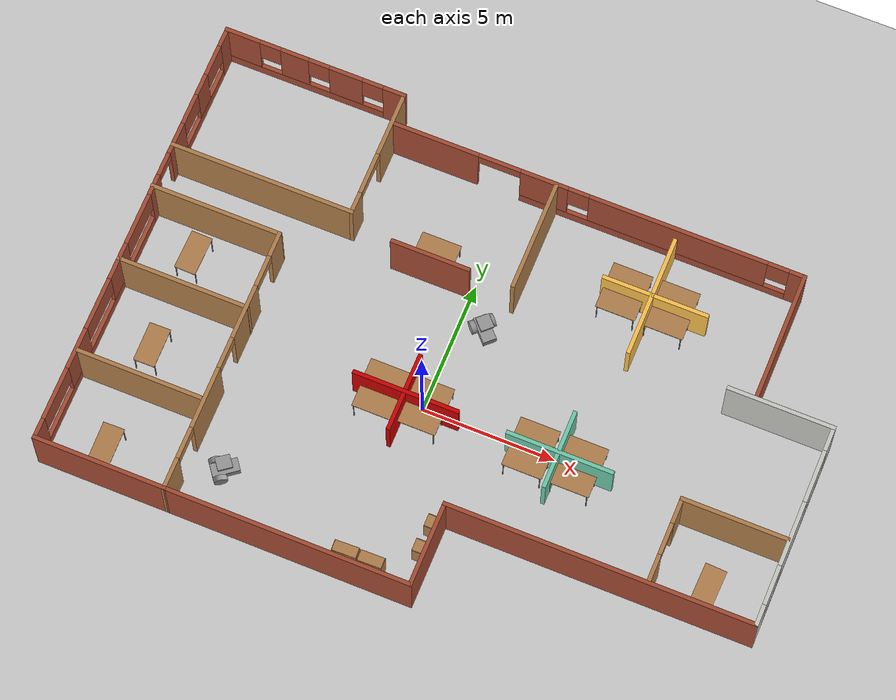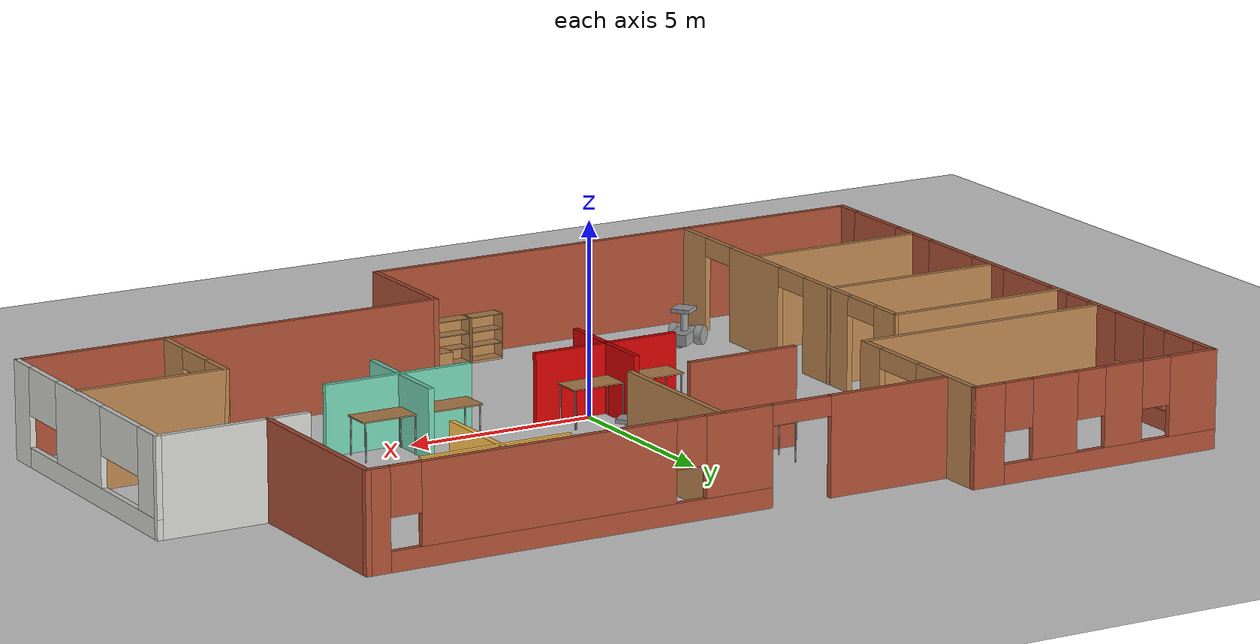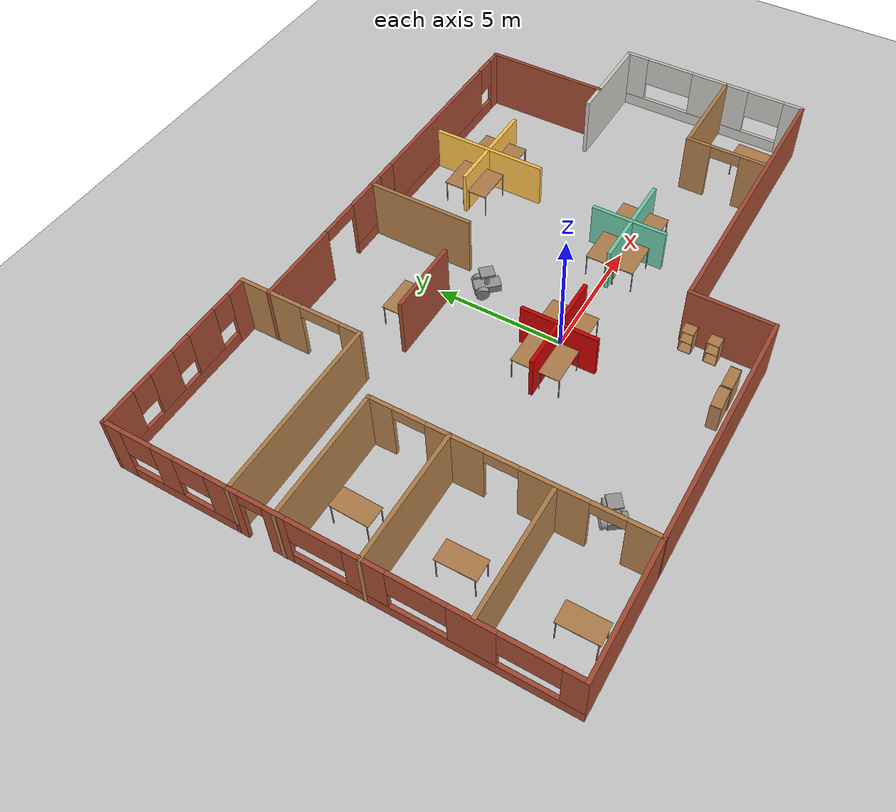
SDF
<sdf version="1.6">
 <world name="default">
  <light name="sun" type="directional">
   <pose>0 0 10 0 -0 0</pose>
   <diffuse>0.8 0.8 0.8 1</diffuse>
   <specular>0.1 0.1 0.1 1</specular>
   <attenuation>
    <range>1000</range>
    <constant>0.9</constant>
    <linear>0.01</linear>
    <quadratic>0.001</quadratic>
   </attenuation>
   <direction>-0.5 0.5 -1</direction>
  </light>
  <model name="ground_plane">
   <static>1</static>
   <link name="link">
    <collision name="collision">
     <geometry><plane><normal>0 0 1</normal><size>100 100</size></plane></geometry>
     <surface><friction><ode><mu>100</mu><mu2>50</mu2></ode></friction></surface>
    </collision>
    <visual name="visual">
     <cast_shadows>0</cast_shadows>
     <geometry><plane><normal>0 0 1</normal><size>100 100</size></plane></geometry>
     <material>
      <script><uri>file://media/materials/scripts/gazebo.material</uri><name>Gazebo/Grey</name></script>
     </material>
    </visual>
   </link>
  </model>
  <gravity>0 0 -9.8</gravity>
  <magnetic_field>6e-06 2.3e-05 -4.2e-05</magnetic_field>
  <atmosphere type="adiabatic"/>
  <physics name="default_physics" default="0" type="ode">
   <max_step_size>0.001</max_step_size>
   <real_time_factor>1</real_time_factor>
   <real_time_update_rate>1000</real_time_update_rate>
  </physics>
  <scene><ambient>0.4 0.4 0.4 1</ambient><background>0.7 0.7 0.7 1</background><shadows>1</shadows></scene>
  <spherical_coordinates>
   <surface_model>EARTH_WGS84</surface_model>
   <latitude_deg>0</latitude_deg>
   <longitude_deg>0</longitude_deg>
   <elevation>0</elevation>
   <heading_deg>0</heading_deg>
  </spherical_coordinates>
  <model name="office">
   <pose>1.02249 1.58575 0 0 -0 0</pose>
   <link name="Wall_0">
    <pose>-12.6413 5.92507 0 0 -0 -1.5708</pose>
    <visual name="Wall_0_Visual_0">
     <pose>-2.10102 0 1.25 0 -0 0</pose>
     <geometry><box><size>0.79796 0.15 2.5</size></box></geometry>
     <material>
      <script><uri>file://media/materials/scripts/gazebo.material</uri><name>Gazebo/Bricks</name></script>
      <ambient>1 1 1 1</ambient>
     </material>
     <meta><layer>0</layer></meta>
    </visual>
    <collision name="Wall_0_Collision_0">
     <geometry><box><size>0.79796 0.15 2.5</size></box></geometry>
     <pose>-2.10102 0 1.25 0 -0 0</pose>
    </collision>
    <visual name="Wall_0_Visual_1">
     <pose>0.39898 0 0.25 0 -0 0</pose>
     <geometry><box><size>4.20204 0.15 0.5</size></box></geometry>
     <material>
      <script><uri>file://media/materials/scripts/gazebo.material</uri><name>Gazebo/Bricks</name></script>
      <ambient>1 1 1 1</ambient>
     </material>
     <meta><layer>0</layer></meta>
    </visual>
    <collision name="Wall_0_Collision_1">
     <geometry><box><size>4.20204 0.15 0.5</size></box></geometry>
     <pose>0.39898 0 0.25 0 -0 0</pose>
    </collision>
    <visual name="Wall_0_Visual_2">
     <pose>-0.076315 0 1.5 0 -0 0</pose>
     <geometry><box><size>0.851451 0.15 2</size></box></geometry>
     <material>
      <script><uri>file://media/materials/scripts/gazebo.material</uri><name>Gazebo/Bricks</name></script>
      <ambient>1 1 1 1</ambient>
     </material>
     <meta><layer>0</layer></meta>
    </visual>
    <collision name="Wall_0_Collision_2">
     <geometry><box><size>0.851451 0.15 2</size></box></geometry>
     <pose>-0.076315 0 1.5 0 -0 0</pose>
    </collision>
    <visual name="Wall_0_Visual_3">
     <pose>2.0247 0 1.5 0 -0 0</pose>
     <geometry><box><size>0.95059 0.15 2</size></box></geometry>
     <material>
      <script><uri>file://media/materials/scripts/gazebo.material</uri><name>Gazebo/Bricks</name></script>
      <ambient>1 1 1 1</ambient>
     </material>
     <meta><layer>0</layer></meta>
    </visual>
    <collision name="Wall_0_Collision_3">
     <geometry><box><size>0.95059 0.15 2</size></box></geometry>
     <pose>2.0247 0 1.5 0 -0 0</pose>
    </collision>
    <visual name="Wall_0_Visual_4">
     <pose>-1.10204 0 1.9 0 -0 0</pose>
     <geometry><box><size>1.2 0.15 1.2</size></box></geometry>
     <material>
      <script><uri>file://media/materials/scripts/gazebo.material</uri><name>Gazebo/Bricks</name></script>
      <ambient>1 1 1 1</ambient>
     </material>
     <meta><layer>0</layer></meta>
    </visual>
    <collision name="Wall_0_Collision_4">
     <geometry><box><size>1.2 0.15 1.2</size></box></geometry>
     <pose>-1.10204 0 1.9 0 -0 0</pose>
    </collision>
    <visual name="Wall_0_Visual_5">
     <pose>0.94941 0 1.9 0 -0 0</pose>
     <geometry><box><size>1.2 0.15 1.2</size></box></geometry>
     <material>
      <script><uri>file://media/materials/scripts/gazebo.material</uri><name>Gazebo/Bricks</name></script>
      <ambient>1 1 1 1</ambient>
     </material>
     <meta><layer>0</layer></meta>
    </visual>
    <collision name="Wall_0_Collision_5">
     <geometry><box><size>1.2 0.15 1.2</size></box></geometry>
     <pose>0.94941 0 1.9 0 -0 0</pose>
    </collision>
   </link>
   <link name="Wall_1">
    <collision name="Wall_1_Collision">
     <geometry><box><size>7 0.15 2.5</size></box></geometry>
     <pose>0 0 1.25 0 -0 0</pose>
    </collision>
    <visual name="Wall_1_Visual">
     <pose>0 0 1.25 0 -0 0</pose>
     <geometry><box><size>7 0.15 2.5</size></box></geometry>
     <material>
      <script><uri>file://media/materials/scripts/gazebo.material</uri><name>Gazebo/Wood</name></script>
      <ambient>1 1 1 1</ambient>
     </material>
     <meta><layer>0</layer></meta>
    </visual>
    <pose>-9.21631 3.50007 0 0 -0 0</pose>
   </link>
   <link name="Wall_12">
    <collision name="Wall_12_Collision">
     <geometry><box><size>4.75 0.15 2.5</size></box></geometry>
     <pose>0 0 1.25 0 -0 0</pose>
    </collision>
    <visual name="Wall_12_Visual">
     <pose>0 0 1.25 0 -0 0</pose>
     <geometry><box><size>4.75 0.15 2.5</size></box></geometry>
     <material>
      <script><uri>file://media/materials/scripts/gazebo.material</uri><name>Gazebo/Wood</name></script>
      <ambient>1 1 1 1</ambient>
     </material>
     <meta><layer>0</layer></meta>
    </visual>
    <pose>-10.2516 -4.8726 0 0 -0 0</pose>
   </link>
   <link name="Wall_19">
    <collision name="Wall_19_Collision">
     <geometry><box><size>5 0.15 2.5</size></box></geometry>
     <pose>0 0 1.25 0 -0 0</pose>
    </collision>
    <visual name="Wall_19_Visual">
     <pose>0 0 1.25 0 -0 0</pose>
     <geometry><box><size>5 0.15 2.5</size></box></geometry>
     <material>
      <script><uri>file://media/materials/scripts/gazebo.material</uri><name>Gazebo/Wood</name></script>
      <ambient>1 1 1 1</ambient>
     </material>
     <meta><layer>0</layer></meta>
    </visual>
    <pose>-10.2173 -1.19338 0 0 -0 0</pose>
   </link>
   <link name="Wall_2">
    <pose>-5.79131 5.92507 0 0 -0 1.5708</pose>
    <visual name="Wall_2_Visual_0">
     <pose>-2.06484 0 1.25 0 -0 0</pose>
     <geometry><box><size>0.870327 0.15 2.5</size></box></geometry>
     <material>
      <script><uri>file://media/materials/scripts/gazebo.material</uri><name>Gazebo/Wood</name></script>
      <ambient>1 1 1 1</ambient>
     </material>
     <meta><layer>0</layer></meta>
    </visual>
    <collision name="Wall_2_Collision_0">
     <geometry><box><size>0.870327 0.15 2.5</size></box></geometry>
     <pose>-2.06484 0 1.25 0 -0 0</pose>
    </collision>
    <visual name="Wall_2_Visual_1">
     <pose>1.23516 0 1.25 0 -0 0</pose>
     <geometry><box><size>2.52967 0.15 2.5</size></box></geometry>
     <material>
      <script><uri>file://media/materials/scripts/gazebo.material</uri><name>Gazebo/Wood</name></script>
      <ambient>1 1 1 1</ambient>
     </material>
     <meta><layer>0</layer></meta>
    </visual>
    <collision name="Wall_2_Collision_1">
     <geometry><box><size>2.52967 0.15 2.5</size></box></geometry>
     <pose>1.23516 0 1.25 0 -0 0</pose>
    </collision>
    <visual name="Wall_2_Visual_2">
     <pose>-0.829673 0 2.25 0 -0 0</pose>
     <geometry><box><size>1.6 0.15 0.5</size></box></geometry>
     <material>
      <script><uri>file://media/materials/scripts/gazebo.material</uri><name>Gazebo/Wood</name></script>
      <ambient>1 1 1 1</ambient>
     </material>
     <meta><layer>0</layer></meta>
    </visual>
    <collision name="Wall_2_Collision_2">
     <geometry><box><size>1.6 0.15 0.5</size></box></geometry>
     <pose>-0.829673 0 2.25 0 -0 0</pose>
    </collision>
   </link>
   <link name="Wall_21">
    <collision name="Wall_21_Collision">
     <geometry><box><size>9.25 0.15 2.5</size></box></geometry>
     <pose>0 0 1.25 0 -0 0</pose>
    </collision>
    <visual name="Wall_21_Visual">
     <pose>0 0 1.25 0 -0 0</pose>
     <geometry><box><size>9.25 0.15 2.5</size></box></geometry>
     <material>
      <script><uri>file://media/materials/scripts/gazebo.material</uri><name>Gazebo/Bricks</name></script>
      <ambient>1 1 1 1</ambient>
     </material>
     <meta><layer>0</layer></meta>
    </visual>
    <pose>-3.24131 -8.34993 0 0 -0 0</pose>
   </link>
   <link name="Wall_22">
    <collision name="Wall_22_Collision">
     <geometry><box><size>3.25 0.15 2.5</size></box></geometry>
     <pose>0 0 1.25 0 -0 0</pose>
    </collision>
    <visual name="Wall_22_Visual">
     <pose>0 0 1.25 0 -0 0</pose>
     <geometry><box><size>3.25 0.15 2.5</size></box></geometry>
     <material>
      <script><uri>file://media/materials/scripts/gazebo.material</uri><name>Gazebo/Bricks</name></script>
      <ambient>1 1 1 1</ambient>
     </material>
     <meta><layer>0</layer></meta>
    </visual>
    <pose>1.30869 -6.79992 0 0 -0 1.5708</pose>
   </link>
   <link name="Wall_23">
    <collision name="Wall_23_Collision">
     <geometry><box><size>11.5 0.15 2.5</size></box></geometry>
     <pose>0 0 1.25 0 -0 0</pose>
    </collision>
    <visual name="Wall_23_Visual">
     <pose>0 0 1.25 0 -0 0</pose>
     <geometry><box><size>11.5 0.15 2.5</size></box></geometry>
     <material>
      <script><uri>file://media/materials/scripts/gazebo.material</uri><name>Gazebo/Bricks</name></script>
      <ambient>1 1 1 1</ambient>
     </material>
     <meta><layer>0</layer></meta>
    </visual>
    <pose>6.98369 -5.24993 0 0 -0 0</pose>
   </link>
   <link name="Wall_24">
    <pose>12.6587 -1.44992 0 0 -0 1.5708</pose>
    <visual name="Wall_24_Visual_0">
     <pose>-3.45904 0 1.25 0 -0 0</pose>
     <geometry><box><size>0.831925 0.15 2.5</size></box></geometry>
     <material>
      <script><uri>file://media/materials/scripts/gazebo.material</uri><name>Gazebo/CeilingTiled</name></script>
      <ambient>1 1 1 1</ambient>
     </material>
     <meta><layer>0</layer></meta>
    </visual>
    <collision name="Wall_24_Collision_0">
     <geometry><box><size>0.831925 0.15 2.5</size></box></geometry>
     <pose>-3.45904 0 1.25 0 -0 0</pose>
    </collision>
    <visual name="Wall_24_Visual_1">
     <pose>0.415962 0 0.25 0 -0 0</pose>
     <geometry><box><size>6.91807 0.15 0.5</size></box></geometry>
     <material>
      <script><uri>file://media/materials/scripts/gazebo.material</uri><name>Gazebo/CeilingTiled</name></script>
      <ambient>1 1 1 1</ambient>
     </material>
     <meta><layer>0</layer></meta>
    </visual>
    <collision name="Wall_24_Collision_1">
     <geometry><box><size>6.91807 0.15 0.5</size></box></geometry>
     <pose>0.415962 0 0.25 0 -0 0</pose>
    </collision>
    <visual name="Wall_24_Visual_2">
     <pose>-0.320599 0 1.5 0 -0 0</pose>
     <geometry><box><size>2.44495 0.15 2</size></box></geometry>
     <material>
      <script><uri>file://media/materials/scripts/gazebo.material</uri><name>Gazebo/CeilingTiled</name></script>
      <ambient>1 1 1 1</ambient>
     </material>
     <meta><layer>0</layer></meta>
    </visual>
    <collision name="Wall_24_Collision_2">
     <geometry><box><size>2.44495 0.15 2</size></box></geometry>
     <pose>-0.320599 0 1.5 0 -0 0</pose>
    </collision>
    <visual name="Wall_24_Visual_3">
     <pose>3.38844 0 1.5 0 -0 0</pose>
     <geometry><box><size>0.973122 0.15 2</size></box></geometry>
     <material>
      <script><uri>file://media/materials/scripts/gazebo.material</uri><name>Gazebo/CeilingTiled</name></script>
      <ambient>1 1 1 1</ambient>
     </material>
     <meta><layer>0</layer></meta>
    </visual>
    <collision name="Wall_24_Collision_3">
     <geometry><box><size>0.973122 0.15 2</size></box></geometry>
     <pose>3.38844 0 1.5 0 -0 0</pose>
    </collision>
    <visual name="Wall_24_Visual_4">
     <pose>-2.29307 0 1.9 0 -0 0</pose>
     <geometry><box><size>1.5 0.15 1.2</size></box></geometry>
     <material>
      <script><uri>file://media/materials/scripts/gazebo.material</uri><name>Gazebo/CeilingTiled</name></script>
      <ambient>1 1 1 1</ambient>
     </material>
     <meta><layer>0</layer></meta>
    </visual>
    <collision name="Wall_24_Collision_4">
     <geometry><box><size>1.5 0.15 1.2</size></box></geometry>
     <pose>-2.29307 0 1.9 0 -0 0</pose>
    </collision>
    <visual name="Wall_24_Visual_5">
     <pose>1.90188 0 1.9 0 -0 0</pose>
     <geometry><box><size>2 0.15 1.2</size></box></geometry>
     <material>
      <script><uri>file://media/materials/scripts/gazebo.material</uri><name>Gazebo/CeilingTiled</name></script>
      <ambient>1 1 1 1</ambient>
     </material>
     <meta><layer>0</layer></meta>
    </visual>
    <collision name="Wall_24_Collision_5">
     <geometry><box><size>2 0.15 1.2</size></box></geometry>
     <pose>1.90188 0 1.9 0 -0 0</pose>
    </collision>
   </link>
   <link name="Wall_25">
    <collision name="Wall_25_Collision">
     <geometry><box><size>4 0.15 2.5</size></box></geometry>
     <pose>0 0 1.25 0 -0 0</pose>
    </collision>
    <visual name="Wall_25_Visual">
     <pose>0 0 1.25 0 -0 0</pose>
     <geometry><box><size>4 0.15 2.5</size></box></geometry>
     <material>
      <script><uri>file://media/materials/scripts/gazebo.material</uri><name>Gazebo/CeilingTiled</name></script>
      <ambient>1 1 1 1</ambient>
     </material>
     <meta><layer>0</layer></meta>
    </visual>
    <pose>10.7337 2.35007 0 0 -0 3.14159</pose>
   </link>
   <link name="Wall_27">
    <collision name="Wall_27_Collision">
     <geometry><box><size>4 0.15 2.5</size></box></geometry>
     <pose>0 0 1.25 0 -0 0</pose>
    </collision>
    <visual name="Wall_27_Visual">
     <pose>0 0 1.25 0 -0 0</pose>
     <geometry><box><size>4 0.15 2.5</size></box></geometry>
     <material>
      <script><uri>file://media/materials/scripts/gazebo.material</uri><name>Gazebo/Wood</name></script>
      <ambient>1 1 1 1</ambient>
     </material>
     <meta><layer>0</layer></meta>
    </visual>
    <pose>10.6699 -2.02159 0 0 -0 3.14159</pose>
   </link>
   <link name="Wall_28">
    <pose>8.74488 -3.57159 0 0 -0 -1.5708</pose>
    <visual name="Wall_28_Visual_0">
     <pose>-1.11107 0 1.25 0 -0 0</pose>
     <geometry><box><size>1.02786 0.15 2.5</size></box></geometry>
     <material>
      <script><uri>file://media/materials/scripts/gazebo.material</uri><name>Gazebo/Wood</name></script>
      <ambient>1 1 1 1</ambient>
     </material>
     <meta><layer>0</layer></meta>
    </visual>
    <collision name="Wall_28_Collision_0">
     <geometry><box><size>1.02786 0.15 2.5</size></box></geometry>
     <pose>-1.11107 0 1.25 0 -0 0</pose>
    </collision>
    <visual name="Wall_28_Visual_1">
     <pose>1.11393 0 1.25 0 -0 0</pose>
     <geometry><box><size>1.02214 0.15 2.5</size></box></geometry>
     <material>
      <script><uri>file://media/materials/scripts/gazebo.material</uri><name>Gazebo/Wood</name></script>
      <ambient>1 1 1 1</ambient>
     </material>
     <meta><layer>0</layer></meta>
    </visual>
    <collision name="Wall_28_Collision_1">
     <geometry><box><size>1.02214 0.15 2.5</size></box></geometry>
     <pose>1.11393 0 1.25 0 -0 0</pose>
    </collision>
    <visual name="Wall_28_Visual_2">
     <pose>0.002857 0 2.25 0 -0 0</pose>
     <geometry><box><size>1.2 0.15 0.5</size></box></geometry>
     <material>
      <script><uri>file://media/materials/scripts/gazebo.material</uri><name>Gazebo/Wood</name></script>
      <ambient>1 1 1 1</ambient>
     </material>
     <meta><layer>0</layer></meta>
    </visual>
    <collision name="Wall_28_Collision_2">
     <geometry><box><size>1.2 0.15 0.5</size></box></geometry>
     <pose>0.002857 0 2.25 0 -0 0</pose>
    </collision>
   </link>
   <link name="Wall_3">
    <pose>-9.21631 8.35008 0 0 -0 3.14159</pose>
    <visual name="Wall_3_Visual_0">
     <pose>-3.0632 0 1.25 0 -0 0</pose>
     <geometry><box><size>0.873598 0.15 2.5</size></box></geometry>
     <material>
      <script><uri>file://media/materials/scripts/gazebo.material</uri><name>Gazebo/Bricks</name></script>
      <ambient>1 1 1 1</ambient>
     </material>
     <meta><layer>0</layer></meta>
    </visual>
    <collision name="Wall_3_Collision_0">
     <geometry><box><size>0.873598 0.15 2.5</size></box></geometry>
     <pose>-3.0632 0 1.25 0 -0 0</pose>
    </collision>
    <visual name="Wall_3_Visual_1">
     <pose>0.436799 0 0.25 0 -0 0</pose>
     <geometry><box><size>6.1264 0.15 0.5</size></box></geometry>
     <material>
      <script><uri>file://media/materials/scripts/gazebo.material</uri><name>Gazebo/Bricks</name></script>
      <ambient>1 1 1 1</ambient>
     </material>
     <meta><layer>0</layer></meta>
    </visual>
    <collision name="Wall_3_Collision_1">
     <geometry><box><size>6.1264 0.15 0.5</size></box></geometry>
     <pose>0.436799 0 0.25 0 -0 0</pose>
    </collision>
    <visual name="Wall_3_Visual_2">
     <pose>-1.18753 0 1.5 0 -0 0</pose>
     <geometry><box><size>1.27775 0.15 2</size></box></geometry>
     <material>
      <script><uri>file://media/materials/scripts/gazebo.material</uri><name>Gazebo/Bricks</name></script>
      <ambient>1 1 1 1</ambient>
     </material>
     <meta><layer>0</layer></meta>
    </visual>
    <collision name="Wall_3_Collision_2">
     <geometry><box><size>1.27775 0.15 2</size></box></geometry>
     <pose>-1.18753 0 1.5 0 -0 0</pose>
    </collision>
    <visual name="Wall_3_Visual_3">
     <pose>0.791597 0 1.5 0 -0 0</pose>
     <geometry><box><size>1.0805 0.15 2</size></box></geometry>
     <material>
      <script><uri>file://media/materials/scripts/gazebo.material</uri><name>Gazebo/Bricks</name></script>
      <ambient>1 1 1 1</ambient>
     </material>
     <meta><layer>0</layer></meta>
    </visual>
    <collision name="Wall_3_Collision_3">
     <geometry><box><size>1.0805 0.15 2</size></box></geometry>
     <pose>0.791597 0 1.5 0 -0 0</pose>
    </collision>
    <visual name="Wall_3_Visual_4">
     <pose>2.81592 0 1.5 0 -0 0</pose>
     <geometry><box><size>1.36816 0.15 2</size></box></geometry>
     <material>
      <script><uri>file://media/materials/scripts/gazebo.material</uri><name>Gazebo/Bricks</name></script>
      <ambient>1 1 1 1</ambient>
     </material>
     <meta><layer>0</layer></meta>
    </visual>
    <collision name="Wall_3_Collision_4">
     <geometry><box><size>1.36816 0.15 2</size></box></geometry>
     <pose>2.81592 0 1.5 0 -0 0</pose>
    </collision>
    <visual name="Wall_3_Visual_5">
     <pose>-2.2264 0 1.9 0 -0 0</pose>
     <geometry><box><size>0.8 0.15 1.2</size></box></geometry>
     <material>
      <script><uri>file://media/materials/scripts/gazebo.material</uri><name>Gazebo/Bricks</name></script>
      <ambient>1 1 1 1</ambient>
     </material>
     <meta><layer>0</layer></meta>
    </visual>
    <collision name="Wall_3_Collision_5">
     <geometry><box><size>0.8 0.15 1.2</size></box></geometry>
     <pose>-2.2264 0 1.9 0 -0 0</pose>
    </collision>
    <visual name="Wall_3_Visual_6">
     <pose>-0.148651 0 1.9 0 -0 0</pose>
     <geometry><box><size>0.8 0.15 1.2</size></box></geometry>
     <material>
      <script><uri>file://media/materials/scripts/gazebo.material</uri><name>Gazebo/Bricks</name></script>
      <ambient>1 1 1 1</ambient>
     </material>
     <meta><layer>0</layer></meta>
    </visual>
    <collision name="Wall_3_Collision_6">
     <geometry><box><size>0.8 0.15 1.2</size></box></geometry>
     <pose>-0.148651 0 1.9 0 -0 0</pose>
    </collision>
    <visual name="Wall_3_Visual_7">
     <pose>1.73185 0 1.9 0 -0 0</pose>
     <geometry><box><size>0.8 0.15 1.2</size></box></geometry>
     <material>
      <script><uri>file://media/materials/scripts/gazebo.material</uri><name>Gazebo/Bricks</name></script>
      <ambient>1 1 1 1</ambient>
     </material>
     <meta><layer>0</layer></meta>
    </visual>
    <collision name="Wall_3_Collision_7">
     <geometry><box><size>0.8 0.15 1.2</size></box></geometry>
     <pose>1.73185 0 1.9 0 -0 0</pose>
    </collision>
   </link>
   <link name="Wall_30">
    <collision name="Wall_30_Collision">
     <geometry><box><size>5 0.15 2.5</size></box></geometry>
     <pose>0 0 1.25 0 -0 0</pose>
    </collision>
    <visual name="Wall_30_Visual">
     <pose>0 0 1.25 0 -0 0</pose>
     <geometry><box><size>5 0.15 2.5</size></box></geometry>
     <material>
      <script><uri>file://media/materials/scripts/gazebo.material</uri><name>Gazebo/Bricks</name></script>
      <ambient>1 1 1 1</ambient>
     </material>
     <meta><layer>0</layer></meta>
    </visual>
    <pose>9.80511 4.78099 0 0 -0 1.5708</pose>
   </link>
   <link name="Wall_31">
    <pose>2.00511 7.20599 0 0 -0 3.14159</pose>
    <visual name="Wall_31_Visual_0">
     <pose>-7.55649 0 1.25 0 -0 0</pose>
     <geometry><box><size>0.637024 0.15 2.5</size></box></geometry>
     <material>
      <script><uri>file://media/materials/scripts/gazebo.material</uri><name>Gazebo/Bricks</name></script>
      <ambient>1 1 1 1</ambient>
     </material>
     <meta><layer>0</layer></meta>
    </visual>
    <collision name="Wall_31_Collision_0">
     <geometry><box><size>0.637024 0.15 2.5</size></box></geometry>
     <pose>-7.55649 0 1.25 0 -0 0</pose>
    </collision>
    <visual name="Wall_31_Visual_1">
     <pose>6.16793 0 1.25 0 -0 0</pose>
     <geometry><box><size>3.41413 0.15 2.5</size></box></geometry>
     <material>
      <script><uri>file://media/materials/scripts/gazebo.material</uri><name>Gazebo/Bricks</name></script>
      <ambient>1 1 1 1</ambient>
     </material>
     <meta><layer>0</layer></meta>
    </visual>
    <collision name="Wall_31_Collision_1">
     <geometry><box><size>3.41413 0.15 2.5</size></box></geometry>
     <pose>6.16793 0 1.25 0 -0 0</pose>
    </collision>
    <visual name="Wall_31_Visual_2">
     <pose>-2.18855 0 0.25 0 -0 0</pose>
     <geometry><box><size>10.0988 0.15 0.5</size></box></geometry>
     <material>
      <script><uri>file://media/materials/scripts/gazebo.material</uri><name>Gazebo/Bricks</name></script>
      <ambient>1 1 1 1</ambient>
     </material>
     <meta><layer>0</layer></meta>
    </visual>
    <collision name="Wall_31_Collision_2">
     <geometry><box><size>10.0988 0.15 0.5</size></box></geometry>
     <pose>-2.18855 0 0.25 0 -0 0</pose>
    </collision>
    <visual name="Wall_31_Visual_3">
     <pose>-3.09013 0 1.5 0 -0 0</pose>
     <geometry><box><size>6.69569 0.15 2</size></box></geometry>
     <material>
      <script><uri>file://media/materials/scripts/gazebo.material</uri><name>Gazebo/Bricks</name></script>
      <ambient>1 1 1 1</ambient>
     </material>
     <meta><layer>0</layer></meta>
    </visual>
    <collision name="Wall_31_Collision_3">
     <geometry><box><size>6.69569 0.15 2</size></box></geometry>
     <pose>-3.09013 0 1.5 0 -0 0</pose>
    </collision>
    <visual name="Wall_31_Visual_4">
     <pose>1.95929 0 1.5 0 -0 0</pose>
     <geometry><box><size>1.80316 0.15 2</size></box></geometry>
     <material>
      <script><uri>file://media/materials/scripts/gazebo.material</uri><name>Gazebo/Bricks</name></script>
      <ambient>1 1 1 1</ambient>
     </material>
     <meta><layer>0</layer></meta>
    </visual>
    <collision name="Wall_31_Collision_4">
     <geometry><box><size>1.80316 0.15 2</size></box></geometry>
     <pose>1.95929 0 1.5 0 -0 0</pose>
    </collision>
    <visual name="Wall_31_Visual_5">
     <pose>-6.83798 0 1.9 0 -0 0</pose>
     <geometry><box><size>0.8 0.15 1.2</size></box></geometry>
     <material>
      <script><uri>file://media/materials/scripts/gazebo.material</uri><name>Gazebo/Bricks</name></script>
      <ambient>1 1 1 1</ambient>
     </material>
     <meta><layer>0</layer></meta>
    </visual>
    <collision name="Wall_31_Collision_5">
     <geometry><box><size>0.8 0.15 1.2</size></box></geometry>
     <pose>-6.83798 0 1.9 0 -0 0</pose>
    </collision>
    <visual name="Wall_31_Visual_6">
     <pose>0.657708 0 1.9 0 -0 0</pose>
     <geometry><box><size>0.8 0.15 1.2</size></box></geometry>
     <material>
      <script><uri>file://media/materials/scripts/gazebo.material</uri><name>Gazebo/Bricks</name></script>
      <ambient>1 1 1 1</ambient>
     </material>
     <meta><layer>0</layer></meta>
    </visual>
    <collision name="Wall_31_Collision_6">
     <geometry><box><size>0.8 0.15 1.2</size></box></geometry>
     <pose>0.657708 0 1.9 0 -0 0</pose>
    </collision>
    <visual name="Wall_31_Visual_7">
     <pose>3.66087 0 2.25 0 -0 0</pose>
     <geometry><box><size>1.6 0.15 0.5</size></box></geometry>
     <material>
      <script><uri>file://media/materials/scripts/gazebo.material</uri><name>Gazebo/Bricks</name></script>
      <ambient>1 1 1 1</ambient>
     </material>
     <meta><layer>0</layer></meta>
    </visual>
    <collision name="Wall_31_Collision_7">
     <geometry><box><size>1.6 0.15 0.5</size></box></geometry>
     <pose>3.66087 0 2.25 0 -0 0</pose>
    </collision>
   </link>
   <link name="Wall_33">
    <collision name="Wall_33_Collision">
     <geometry><box><size>4.25 0.15 2.5</size></box></geometry>
     <pose>0 0 1.25 0 -0 0</pose>
    </collision>
    <visual name="Wall_33_Visual">
     <pose>0 0 1.25 0 -0 0</pose>
     <geometry><box><size>4.25 0.15 2.5</size></box></geometry>
     <material>
      <script><uri>file://media/materials/scripts/gazebo.material</uri><name>Gazebo/Wood</name></script>
      <ambient>1 1 1 1</ambient>
     </material>
     <meta><layer>0</layer></meta>
    </visual>
    <pose>0.500764 5.12338 0 0 -0 -1.5708</pose>
   </link>
   <link name="Wall_35">
    <collision name="Wall_35_Collision">
     <geometry><box><size>4.75 0.15 1.8</size></box></geometry>
     <pose>0 0 0.9 0 -0 0</pose>
    </collision>
    <visual name="Wall_35_Visual">
     <pose>0 0 0.9 0 -0 0</pose>
     <geometry><box><size>4.75 0.15 1.8</size></box></geometry>
     <material>
      <script><uri>file://media/materials/scripts/gazebo.material</uri><name>Gazebo/Grey</name></script>
      <ambient>1 0.764706 0.305882 1</ambient>
     </material>
     <meta><layer>0</layer></meta>
    </visual>
    <pose>5.05557 4.85856 0 0 -0 -1.5708</pose>
   </link>
   <link name="Wall_37">
    <collision name="Wall_37_Collision">
     <geometry><box><size>4 0.15 1.8</size></box></geometry>
     <pose>0 0 0.9 0 -0 0</pose>
    </collision>
    <visual name="Wall_37_Visual">
     <pose>0 0 0.9 0 -0 0</pose>
     <geometry><box><size>4 0.15 1.8</size></box></geometry>
     <material>
      <script><uri>file://media/materials/scripts/gazebo.material</uri><name>Gazebo/Grey</name></script>
      <ambient>1 0.764706 0.305882 1</ambient>
     </material>
     <meta><layer>0</layer></meta>
    </visual>
    <pose>5.17957 4.83056 0 0 -0 0</pose>
   </link>
   <link name="Wall_39">
    <collision name="Wall_39_Collision">
     <geometry><box><size>3 0.15 2.5</size></box></geometry>
     <pose>0 0 1.25 0 -0 0</pose>
    </collision>
    <visual name="Wall_39_Visual">
     <pose>0 0 1.25 0 -0 0</pose>
     <geometry><box><size>3 0.15 2.5</size></box></geometry>
     <material>
      <script><uri>file://media/materials/scripts/gazebo.material</uri><name>Gazebo/Bricks</name></script>
      <ambient>1 1 1 1</ambient>
     </material>
     <meta><layer>0</layer></meta>
    </visual>
    <pose>-2.60246 3.02942 0 0 -0 3.14159</pose>
   </link>
   <link name="Wall_41">
    <collision name="Wall_41_Collision">
     <geometry><box><size>4 0.15 1.8</size></box></geometry>
     <pose>0 0 0.9 0 -0 0</pose>
    </collision>
    <visual name="Wall_41_Visual">
     <pose>0 0 0.9 0 -0 0</pose>
     <geometry><box><size>4 0.15 1.8</size></box></geometry>
     <material>
      <script><uri>file://media/materials/scripts/gazebo.material</uri><name>Gazebo/Grey</name></script>
      <ambient>0.8 0 0 1</ambient>
     </material>
     <meta><layer>0</layer></meta>
    </visual>
    <pose>-1.56643 -1.75744 0 0 -0 0</pose>
   </link>
   <link name="Wall_43">
    <collision name="Wall_43_Collision">
     <geometry><box><size>3 0.15 1.8</size></box></geometry>
     <pose>0 0 0.9 0 -0 0</pose>
    </collision>
    <visual name="Wall_43_Visual">
     <pose>0 0 0.9 0 -0 0</pose>
     <geometry><box><size>3 0.15 1.8</size></box></geometry>
     <material>
      <script><uri>file://media/materials/scripts/gazebo.material</uri><name>Gazebo/Grey</name></script>
      <ambient>0.8 0 0 1</ambient>
     </material>
     <meta><layer>0</layer></meta>
    </visual>
    <pose>-1.61128 -1.78879 0 0 -0 -1.5708</pose>
   </link>
   <link name="Wall_45">
    <collision name="Wall_45_Collision">
     <geometry><box><size>4 0.15 1.8</size></box></geometry>
     <pose>0 0 0.9 0 -0 0</pose>
    </collision>
    <visual name="Wall_45_Visual">
     <pose>0 0 0.9 0 -0 0</pose>
     <geometry><box><size>4 0.15 1.8</size></box></geometry>
     <material>
      <script><uri>file://media/materials/scripts/gazebo.material</uri><name>Gazebo/Grey</name></script>
      <ambient>0.435294 0.796078 0.67451 1</ambient>
     </material>
     <meta><layer>0</layer></meta>
    </visual>
    <pose>4.20657 -1.80944 0 0 -0 0</pose>
   </link>
   <link name="Wall_47">
    <collision name="Wall_47_Collision">
     <geometry><box><size>3 0.15 1.8</size></box></geometry>
     <pose>0 0 0.9 0 -0 0</pose>
    </collision>
    <visual name="Wall_47_Visual">
     <pose>0 0 0.9 0 -0 0</pose>
     <geometry><box><size>3 0.15 1.8</size></box></geometry>
     <material>
      <script><uri>file://media/materials/scripts/gazebo.material</uri><name>Gazebo/Grey</name></script>
      <ambient>0.435294 0.796078 0.67451 1</ambient>
     </material>
     <meta><layer>0</layer></meta>
    </visual>
    <pose>4.14857 -1.70944 0 0 -0 -1.5708</pose>
   </link>
   <link name="Wall_5">
    <pose>-12.6413 -2.42492 0 0 -0 -1.5708</pose>
    <visual name="Wall_5_Visual_0">
     <pose>-5.7769 0 1.25 0 -0 0</pose>
     <geometry><box><size>0.446198 0.15 2.5</size></box></geometry>
     <material>
      <script><uri>file://media/materials/scripts/gazebo.material</uri><name>Gazebo/Bricks</name></script>
      <ambient>1 1 1 1</ambient>
     </material>
     <meta><layer>0</layer></meta>
    </visual>
    <collision name="Wall_5_Collision_0">
     <geometry><box><size>0.446198 0.15 2.5</size></box></geometry>
     <pose>-5.7769 0 1.25 0 -0 0</pose>
    </collision>
    <visual name="Wall_5_Visual_1">
     <pose>-4.24561 0 1.25 0 -0 0</pose>
     <geometry><box><size>0.816375 0.15 2.5</size></box></geometry>
     <material>
      <script><uri>file://media/materials/scripts/gazebo.material</uri><name>Gazebo/Bricks</name></script>
      <ambient>1 1 1 1</ambient>
     </material>
     <meta><layer>0</layer></meta>
    </visual>
    <collision name="Wall_5_Collision_1">
     <geometry><box><size>0.816375 0.15 2.5</size></box></geometry>
     <pose>-4.24561 0 1.25 0 -0 0</pose>
    </collision>
    <visual name="Wall_5_Visual_2">
     <pose>1.08129 0 0.25 0 -0 0</pose>
     <geometry><box><size>9.83743 0.15 0.5</size></box></geometry>
     <material>
      <script><uri>file://media/materials/scripts/gazebo.material</uri><name>Gazebo/Bricks</name></script>
      <ambient>1 1 1 1</ambient>
     </material>
     <meta><layer>0</layer></meta>
    </visual>
    <collision name="Wall_5_Collision_2">
     <geometry><box><size>9.83743 0.15 0.5</size></box></geometry>
     <pose>1.08129 0 0.25 0 -0 0</pose>
    </collision>
    <visual name="Wall_5_Visual_3">
     <pose>-1.11473 0 1.5 0 -0 0</pose>
     <geometry><box><size>1.44538 0.15 2</size></box></geometry>
     <material>
      <script><uri>file://media/materials/scripts/gazebo.material</uri><name>Gazebo/Bricks</name></script>
      <ambient>1 1 1 1</ambient>
     </material>
     <meta><layer>0</layer></meta>
    </visual>
    <collision name="Wall_5_Collision_3">
     <geometry><box><size>1.44538 0.15 2</size></box></geometry>
     <pose>-1.11473 0 1.5 0 -0 0</pose>
    </collision>
    <visual name="Wall_5_Visual_4">
     <pose>2.40298 0 1.5 0 -0 0</pose>
     <geometry><box><size>1.59004 0.15 2</size></box></geometry>
     <material>
      <script><uri>file://media/materials/scripts/gazebo.material</uri><name>Gazebo/Bricks</name></script>
      <ambient>1 1 1 1</ambient>
     </material>
     <meta><layer>0</layer></meta>
    </visual>
    <collision name="Wall_5_Collision_4">
     <geometry><box><size>1.59004 0.15 2</size></box></geometry>
     <pose>2.40298 0 1.5 0 -0 0</pose>
    </collision>
    <visual name="Wall_5_Visual_5">
     <pose>5.599 0 1.5 0 -0 0</pose>
     <geometry><box><size>0.802003 0.15 2</size></box></geometry>
     <material>
      <script><uri>file://media/materials/scripts/gazebo.material</uri><name>Gazebo/Bricks</name></script>
      <ambient>1 1 1 1</ambient>
     </material>
     <meta><layer>0</layer></meta>
    </visual>
    <collision name="Wall_5_Collision_5">
     <geometry><box><size>0.802003 0.15 2</size></box></geometry>
     <pose>5.599 0 1.5 0 -0 0</pose>
    </collision>
    <visual name="Wall_5_Visual_6">
     <pose>-2.83743 0 1.9 0 -0 0</pose>
     <geometry><box><size>2 0.15 1.2</size></box></geometry>
     <material>
      <script><uri>file://media/materials/scripts/gazebo.material</uri><name>Gazebo/Bricks</name></script>
      <ambient>1 1 1 1</ambient>
     </material>
     <meta><layer>0</layer></meta>
    </visual>
    <collision name="Wall_5_Collision_6">
     <geometry><box><size>2 0.15 1.2</size></box></geometry>
     <pose>-2.83743 0 1.9 0 -0 0</pose>
    </collision>
    <visual name="Wall_5_Visual_7">
     <pose>0.607958 0 1.9 0 -0 0</pose>
     <geometry><box><size>2 0.15 1.2</size></box></geometry>
     <material>
      <script><uri>file://media/materials/scripts/gazebo.material</uri><name>Gazebo/Bricks</name></script>
      <ambient>1 1 1 1</ambient>
     </material>
     <meta><layer>0</layer></meta>
    </visual>
    <collision name="Wall_5_Collision_7">
     <geometry><box><size>2 0.15 1.2</size></box></geometry>
     <pose>0.607958 0 1.9 0 -0 0</pose>
    </collision>
    <visual name="Wall_5_Visual_8">
     <pose>4.198 0 1.9 0 -0 0</pose>
     <geometry><box><size>2 0.15 1.2</size></box></geometry>
     <material>
      <script><uri>file://media/materials/scripts/gazebo.material</uri><name>Gazebo/Bricks</name></script>
      <ambient>1 1 1 1</ambient>
     </material>
     <meta><layer>0</layer></meta>
    </visual>
    <collision name="Wall_5_Collision_8">
     <geometry><box><size>2 0.15 1.2</size></box></geometry>
     <pose>4.198 0 1.9 0 -0 0</pose>
    </collision>
    <visual name="Wall_5_Visual_9">
     <pose>-5.1038 0 2.25 0 -0 0</pose>
     <geometry><box><size>0.9 0.15 0.5</size></box></geometry>
     <material>
      <script><uri>file://media/materials/scripts/gazebo.material</uri><name>Gazebo/Bricks</name></script>
      <ambient>1 1 1 1</ambient>
     </material>
     <meta><layer>0</layer></meta>
    </visual>
    <collision name="Wall_5_Collision_9">
     <geometry><box><size>0.9 0.15 0.5</size></box></geometry>
     <pose>-5.1038 0 2.25 0 -0 0</pose>
    </collision>
   </link>
   <link name="Wall_6">
    <collision name="Wall_6_Collision">
     <geometry><box><size>5 0.15 2.5</size></box></geometry>
     <pose>0 0 1.25 0 -0 0</pose>
    </collision>
    <visual name="Wall_6_Visual">
     <pose>0 0 1.25 0 -0 0</pose>
     <geometry><box><size>5 0.15 2.5</size></box></geometry>
     <material>
      <script><uri>file://media/materials/scripts/gazebo.material</uri><name>Gazebo/Bricks</name></script>
      <ambient>1 1 1 1</ambient>
     </material>
     <meta><layer>0</layer></meta>
    </visual>
    <pose>-10.2163 -8.34993 0 0 -0 0</pose>
   </link>
   <link name="Wall_7">
    <pose>-7.8 -3.28797 0 0 -0 1.57251</pose>
    <visual name="Wall_7_Visual_0">
     <pose>-4.52035 0 1.25 0 -0 0</pose>
     <geometry><box><size>1.23327 0.15 2.5</size></box></geometry>
     <material>
      <script><uri>file://media/materials/scripts/gazebo.material</uri><name>Gazebo/Wood</name></script>
      <ambient>0.921569 0.807843 0.615686 1</ambient>
     </material>
     <meta><layer>0</layer></meta>
    </visual>
    <collision name="Wall_7_Collision_0">
     <geometry><box><size>1.23327 0.15 2.5</size></box></geometry>
     <pose>-4.52035 0 1.25 0 -0 0</pose>
    </collision>
    <visual name="Wall_7_Visual_1">
     <pose>-1.52121 0 1.25 0 -0 0</pose>
     <geometry><box><size>2.365 0.15 2.5</size></box></geometry>
     <material>
      <script><uri>file://media/materials/scripts/gazebo.material</uri><name>Gazebo/Wood</name></script>
      <ambient>0.921569 0.807843 0.615686 1</ambient>
     </material>
     <meta><layer>0</layer></meta>
    </visual>
    <collision name="Wall_7_Collision_1">
     <geometry><box><size>2.365 0.15 2.5</size></box></geometry>
     <pose>-1.52121 0 1.25 0 -0 0</pose>
    </collision>
    <visual name="Wall_7_Visual_2">
     <pose>1.90894 0 1.25 0 -0 0</pose>
     <geometry><box><size>2.09531 0.15 2.5</size></box></geometry>
     <material>
      <script><uri>file://media/materials/scripts/gazebo.material</uri><name>Gazebo/Wood</name></script>
      <ambient>0.921569 0.807843 0.615686 1</ambient>
     </material>
     <meta><layer>0</layer></meta>
    </visual>
    <collision name="Wall_7_Collision_2">
     <geometry><box><size>2.09531 0.15 2.5</size></box></geometry>
     <pose>1.90894 0 1.25 0 -0 0</pose>
    </collision>
    <visual name="Wall_7_Visual_3">
     <pose>4.64679 0 1.25 0 -0 0</pose>
     <geometry><box><size>0.980386 0.15 2.5</size></box></geometry>
     <material>
      <script><uri>file://media/materials/scripts/gazebo.material</uri><name>Gazebo/Wood</name></script>
      <ambient>0.921569 0.807843 0.615686 1</ambient>
     </material>
     <meta><layer>0</layer></meta>
    </visual>
    <collision name="Wall_7_Collision_3">
     <geometry><box><size>0.980386 0.15 2.5</size></box></geometry>
     <pose>4.64679 0 1.25 0 -0 0</pose>
    </collision>
    <visual name="Wall_7_Visual_4">
     <pose>-3.30371 0 2.25 0 -0 0</pose>
     <geometry><box><size>1.2 0.15 0.5</size></box></geometry>
     <material>
      <script><uri>file://media/materials/scripts/gazebo.material</uri><name>Gazebo/Wood</name></script>
      <ambient>0.921569 0.807843 0.615686 1</ambient>
     </material>
     <meta><layer>0</layer></meta>
    </visual>
    <collision name="Wall_7_Collision_4">
     <geometry><box><size>1.2 0.15 0.5</size></box></geometry>
     <pose>-3.30371 0 2.25 0 -0 0</pose>
    </collision>
    <visual name="Wall_7_Visual_5">
     <pose>0.26129 0 2.25 0 -0 0</pose>
     <geometry><box><size>1.2 0.15 0.5</size></box></geometry>
     <material>
      <script><uri>file://media/materials/scripts/gazebo.material</uri><name>Gazebo/Wood</name></script>
      <ambient>0.921569 0.807843 0.615686 1</ambient>
     </material>
     <meta><layer>0</layer></meta>
    </visual>
    <collision name="Wall_7_Collision_5">
     <geometry><box><size>1.2 0.15 0.5</size></box></geometry>
     <pose>0.26129 0 2.25 0 -0 0</pose>
    </collision>
    <visual name="Wall_7_Visual_6">
     <pose>3.5566 0 2.25 0 -0 0</pose>
     <geometry><box><size>1.2 0.15 0.5</size></box></geometry>
     <material>
      <script><uri>file://media/materials/scripts/gazebo.material</uri><name>Gazebo/Wood</name></script>
      <ambient>0.921569 0.807843 0.615686 1</ambient>
     </material>
     <meta><layer>0</layer></meta>
    </visual>
    <collision name="Wall_7_Collision_6">
     <geometry><box><size>1.2 0.15 0.5</size></box></geometry>
     <pose>3.5566 0 2.25 0 -0 0</pose>
    </collision>
   </link>
   <link name="Wall_8">
    <collision name="Wall_8_Collision">
     <geometry><box><size>5 0.15 2.5</size></box></geometry>
     <pose>0 0 1.25 0 -0 0</pose>
    </collision>
    <visual name="Wall_8_Visual">
     <pose>0 0 1.25 0 -0 0</pose>
     <geometry><box><size>5 0.15 2.5</size></box></geometry>
     <material>
      <script><uri>file://media/materials/scripts/gazebo.material</uri><name>Gazebo/Wood</name></script>
      <ambient>1 1 1 1</ambient>
     </material>
     <meta><layer>0</layer></meta>
    </visual>
    <pose>-10.2337 1.77399 0 0 -0 3.14159</pose>
   </link>
   <static>1</static>
  </model>
  <model name="cody">
   <link name="link_0">
    <inertial>
     <mass>0.139888</mass>
     <inertia>
      <ixx>0.00424815</ixx>
      <ixy>0</ixy>
      <ixz>0</ixz>
      <iyy>0.01242</iyy>
      <iyz>0</iyz>
      <izz>0.0151428</izz>
     </inertia>
    </inertial>
    <pose>2.26803 -0.161715 0.175 0 -0 0</pose>
    <visual name="visual">
     <geometry><box><size>1 0.5 0.3</size></box></geometry>
     <material>
      <lighting>1</lighting>
      <script><uri>file://media/materials/scripts/gazebo.material</uri><name>Gazebo/Grey</name></script>
      <shader type="pixel"><normal_map>__default__</normal_map></shader>
      <ambient>0.3 0.3 0.3 1</ambient>
      <diffuse>0.7 0.7 0.7 1</diffuse>
      <specular>0.01 0.01 0.01 1</specular>
      <emissive>0 0 0 1</emissive>
     </material>
    </visual>
    <collision name="collision">
     <geometry><box><size>1 0.5 0.3</size></box></geometry>
     <surface>
      <friction>
       <ode><mu>1</mu><mu2>1</mu2><fdir1>0 0 0</fdir1><slip1>0</slip1><slip2>0</slip2></ode>
       <torsional>
        <coefficient>1</coefficient>
        <patch_radius>0</patch_radius>
        <surface_radius>0</surface_radius>
        <use_patch_radius>1</use_patch_radius>
        <ode><slip>0</slip></ode>
       </torsional>
      </friction>
      <bounce><restitution_coefficient>0</restitution_coefficient><threshold>1e+06</threshold></bounce>
      <contact>
       <collide_without_contact>0</collide_without_contact>
       <collide_without_contact_bitmask>1</collide_without_contact_bitmask>
       <collide_bitmask>1</collide_bitmask>
       <ode>
        <soft_cfm>0</soft_cfm>
        <soft_erp>0.2</soft_erp>
        <kp>1e+13</kp>
        <kd>1</kd>
        <max_vel>0.01</max_vel>
        <min_depth>0</min_depth>
       </ode>
       <bullet>
        <split_impulse>1</split_impulse>
        <split_impulse_penetration_threshold>-0.01</split_impulse_penetration_threshold>
        <soft_cfm>0</soft_cfm>
        <soft_erp>0.2</soft_erp>
        <kp>1e+13</kp>
        <kd>1</kd>
       </bullet>
      </contact>
     </surface>
    </collision>
   </link>
   <link name="link_1">
    <inertial>
     <mass>1</mass>
     <inertia><ixx>0.1</ixx><ixy>0</ixy><ixz>0</ixz><iyy>0.1</iyy><iyz>0</iyz><izz>0.1</izz></inertia>
    </inertial>
    <pose>1.96803 -0.161715 0.125 0 -0 0</pose>
    <visual name="visual">
     <geometry><sphere><radius>0.2</radius></sphere></geometry>
     <material>
      <lighting>1</lighting>
      <script><uri>file://media/materials/scripts/gazebo.material</uri><name>Gazebo/Grey</name></script>
      <shader type="pixel"><normal_map>__default__</normal_map></shader>
      <ambient>0.3 0.3 0.3 1</ambient>
      <diffuse>0.7 0.7 0.7 1</diffuse>
      <specular>0.01 0.01 0.01 1</specular>
      <emissive>0 0 0 1</emissive>
     </material>
    </visual>
    <collision name="collision">
     <geometry><sphere><radius>0.2</radius></sphere></geometry>
     <surface>
      <friction>
       <ode><mu>1</mu><mu2>1</mu2><fdir1>0 0 0</fdir1><slip1>0</slip1><slip2>0</slip2></ode>
       <torsional>
        <coefficient>1</coefficient>
        <patch_radius>0</patch_radius>
        <surface_radius>0</surface_radius>
        <use_patch_radius>1</use_patch_radius>
        <ode><slip>0</slip></ode>
       </torsional>
      </friction>
      <bounce><restitution_coefficient>0</restitution_coefficient><threshold>1e+06</threshold></bounce>
      <contact>
       <collide_without_contact>0</collide_without_contact>
       <collide_without_contact_bitmask>1</collide_without_contact_bitmask>
       <collide_bitmask>1</collide_bitmask>
       <ode>
        <soft_cfm>0</soft_cfm>
        <soft_erp>0.2</soft_erp>
        <kp>1e+13</kp>
        <kd>1</kd>
        <max_vel>0.01</max_vel>
        <min_depth>0</min_depth>
       </ode>
       <bullet>
        <split_impulse>1</split_impulse>
        <split_impulse_penetration_threshold>-0.01</split_impulse_penetration_threshold>
        <soft_cfm>0</soft_cfm>
        <soft_erp>0.2</soft_erp>
        <kp>1e+13</kp>
        <kd>1</kd>
       </bullet>
      </contact>
     </surface>
    </collision>
   </link>
   <link name="link_2_clone">
    <inertial>
     <mass>1</mass>
     <inertia><ixx>0.145833</ixx><ixy>0</ixy><ixz>0</ixz><iyy>0.145833</iyy><iyz>0</iyz><izz>0.125</izz></inertia>
    </inertial>
    <pose>2.51803 -0.511739 0.175 1.5707 -0 0</pose>
    <visual name="visual">
     <geometry><cylinder><radius>0.25</radius><length>0.2</length></cylinder></geometry>
     <material>
      <lighting>1</lighting>
      <script><uri>file://media/materials/scripts/gazebo.material</uri><name>Gazebo/Grey</name></script>
      <shader type="pixel"><normal_map>__default__</normal_map></shader>
      <ambient>0.3 0.3 0.3 1</ambient>
      <diffuse>0.7 0.7 0.7 1</diffuse>
      <specular>0.01 0.01 0.01 1</specular>
      <emissive>0 0 0 1</emissive>
     </material>
    </visual>
    <collision name="collision">
     <geometry><cylinder><radius>0.25</radius><length>0.2</length></cylinder></geometry>
     <surface>
      <friction>
       <ode><mu>1</mu><mu2>1</mu2><fdir1>0 0 0</fdir1><slip1>0</slip1><slip2>0</slip2></ode>
       <torsional>
        <coefficient>1</coefficient>
        <patch_radius>0</patch_radius>
        <surface_radius>0</surface_radius>
        <use_patch_radius>1</use_patch_radius>
        <ode><slip>0</slip></ode>
       </torsional>
      </friction>
      <bounce><restitution_coefficient>0</restitution_coefficient><threshold>1e+06</threshold></bounce>
      <contact>
       <collide_without_contact>0</collide_without_contact>
       <collide_without_contact_bitmask>1</collide_without_contact_bitmask>
       <collide_bitmask>1</collide_bitmask>
       <ode>
        <soft_cfm>0</soft_cfm>
        <soft_erp>0.2</soft_erp>
        <kp>1e+13</kp>
        <kd>1</kd>
        <max_vel>0.01</max_vel>
        <min_depth>0</min_depth>
       </ode>
       <bullet>
        <split_impulse>1</split_impulse>
        <split_impulse_penetration_threshold>-0.01</split_impulse_penetration_threshold>
        <soft_cfm>0</soft_cfm>
        <soft_erp>0.2</soft_erp>
        <kp>1e+13</kp>
        <kd>1</kd>
       </bullet>
      </contact>
     </surface>
    </collision>
   </link>
   <link name="link_3_clone">
    <inertial>
     <mass>1</mass>
     <inertia><ixx>0.145833</ixx><ixy>0</ixy><ixz>0</ixz><iyy>0.145833</iyy><iyz>0</iyz><izz>0.125</izz></inertia>
    </inertial>
    <pose>2.51803 0.188309 0.175 1.5707 -0 0</pose>
    <visual name="visual">
     <geometry><cylinder><radius>0.25</radius><length>0.2</length></cylinder></geometry>
     <material>
      <lighting>1</lighting>
      <script><uri>file://media/materials/scripts/gazebo.material</uri><name>Gazebo/Grey</name></script>
      <shader type="pixel"><normal_map>__default__</normal_map></shader>
      <ambient>0.3 0.3 0.3 1</ambient>
      <diffuse>0.7 0.7 0.7 1</diffuse>
      <specular>0.01 0.01 0.01 1</specular>
      <emissive>0 0 0 1</emissive>
     </material>
    </visual>
    <collision name="collision">
     <geometry><cylinder><radius>0.25</radius><length>0.2</length></cylinder></geometry>
     <surface>
      <friction>
       <ode><mu>1</mu><mu2>1</mu2><fdir1>0 0 0</fdir1><slip1>0</slip1><slip2>0</slip2></ode>
       <torsional>
        <coefficient>1</coefficient>
        <patch_radius>0</patch_radius>
        <surface_radius>0</surface_radius>
        <use_patch_radius>1</use_patch_radius>
        <ode><slip>0</slip></ode>
       </torsional>
      </friction>
      <bounce><restitution_coefficient>0</restitution_coefficient><threshold>1e+06</threshold></bounce>
      <contact>
       <collide_without_contact>0</collide_without_contact>
       <collide_without_contact_bitmask>1</collide_without_contact_bitmask>
       <collide_bitmask>1</collide_bitmask>
       <ode>
        <soft_cfm>0</soft_cfm>
        <soft_erp>0.2</soft_erp>
        <kp>1e+13</kp>
        <kd>1</kd>
        <max_vel>0.01</max_vel>
        <min_depth>0</min_depth>
       </ode>
       <bullet>
        <split_impulse>1</split_impulse>
        <split_impulse_penetration_threshold>-0.01</split_impulse_penetration_threshold>
        <soft_cfm>0</soft_cfm>
        <soft_erp>0.2</soft_erp>
        <kp>1e+13</kp>
        <kd>1</kd>
       </bullet>
      </contact>
     </surface>
    </collision>
   </link>
   <link name="link_4">
    <inertial>
     <mass>1</mass>
     <inertia><ixx>0.145833</ixx><ixy>0</ixy><ixz>0</ixz><iyy>0.145833</iyy><iyz>0</iyz><izz>0.125</izz></inertia>
    </inertial>
    <pose>2.26803 -0.161715 0.575 0 -0 0</pose>
    <visual name="visual">
     <geometry><cylinder><radius>0.1</radius><length>0.5</length></cylinder></geometry>
     <material>
      <lighting>1</lighting>
      <script><uri>file://media/materials/scripts/gazebo.material</uri><name>Gazebo/Grey</name></script>
      <shader type="pixel"><normal_map>__default__</normal_map></shader>
      <ambient>0.3 0.3 0.3 1</ambient>
      <diffuse>0.7 0.7 0.7 1</diffuse>
      <specular>0.01 0.01 0.01 1</specular>
      <emissive>0 0 0 1</emissive>
     </material>
    </visual>
    <collision name="collision">
     <geometry><cylinder><radius>0.1</radius><length>0.5</length></cylinder></geometry>
     <surface>
      <friction>
       <ode><mu>1</mu><mu2>1</mu2><fdir1>0 0 0</fdir1><slip1>0</slip1><slip2>0</slip2></ode>
       <torsional>
        <coefficient>1</coefficient>
        <patch_radius>0</patch_radius>
        <surface_radius>0</surface_radius>
        <use_patch_radius>1</use_patch_radius>
        <ode><slip>0</slip></ode>
       </torsional>
      </friction>
      <bounce><restitution_coefficient>0</restitution_coefficient><threshold>1e+06</threshold></bounce>
      <contact>
       <collide_without_contact>0</collide_without_contact>
       <collide_without_contact_bitmask>1</collide_without_contact_bitmask>
       <collide_bitmask>1</collide_bitmask>
       <ode>
        <soft_cfm>0</soft_cfm>
        <soft_erp>0.2</soft_erp>
        <kp>1e+13</kp>
        <kd>1</kd>
        <max_vel>0.01</max_vel>
        <min_depth>0</min_depth>
       </ode>
       <bullet>
        <split_impulse>1</split_impulse>
        <split_impulse_penetration_threshold>-0.01</split_impulse_penetration_threshold>
        <soft_cfm>0</soft_cfm>
        <soft_erp>0.2</soft_erp>
        <kp>1e+13</kp>
        <kd>1</kd>
       </bullet>
      </contact>
     </surface>
    </collision>
   </link>
   <link name="link_5_clone">
    <inertial>
     <mass>0.0226706</mass>
     <inertia>
      <ixx>0.00054023</ixx>
      <ixy>0</ixy>
      <ixz>0</ixz>
      <iyy>0.0004373</iyy>
      <iyz>0</iyz>
      <izz>0.00094619</izz>
     </inertia>
    </inertial>
    <pose>2.28803 -0.141715 0.875 0 -0 0</pose>
    <visual name="visual">
     <geometry><box><size>0.5414 0.5 0.1</size></box></geometry>
     <material>
      <lighting>1</lighting>
      <script><uri>file://media/materials/scripts/gazebo.material</uri><name>Gazebo/Grey</name></script>
      <shader type="pixel"><normal_map>__default__</normal_map></shader>
      <ambient>0.3 0.3 0.3 1</ambient>
      <diffuse>0.7 0.7 0.7 1</diffuse>
      <specular>0.01 0.01 0.01 1</specular>
      <emissive>0 0 0 1</emissive>
     </material>
    </visual>
    <collision name="collision">
     <geometry><box><size>0.472414 0.526936 0.091081</size></box></geometry>
     <surface>
      <friction>
       <ode><mu>1</mu><mu2>1</mu2><fdir1>0 0 0</fdir1><slip1>0</slip1><slip2>0</slip2></ode>
       <torsional>
        <coefficient>1</coefficient>
        <patch_radius>0</patch_radius>
        <surface_radius>0</surface_radius>
        <use_patch_radius>1</use_patch_radius>
        <ode><slip>0</slip></ode>
       </torsional>
      </friction>
      <bounce><restitution_coefficient>0</restitution_coefficient><threshold>1e+06</threshold></bounce>
      <contact>
       <collide_without_contact>0</collide_without_contact>
       <collide_without_contact_bitmask>1</collide_without_contact_bitmask>
       <collide_bitmask>1</collide_bitmask>
       <ode>
        <soft_cfm>0</soft_cfm>
        <soft_erp>0.2</soft_erp>
        <kp>1e+13</kp>
        <kd>1</kd>
        <max_vel>0.01</max_vel>
        <min_depth>0</min_depth>
       </ode>
       <bullet>
        <split_impulse>1</split_impulse>
        <split_impulse_penetration_threshold>-0.01</split_impulse_penetration_threshold>
        <soft_cfm>0</soft_cfm>
        <soft_erp>0.2</soft_erp>
        <kp>1e+13</kp>
        <kd>1</kd>
       </bullet>
      </contact>
     </surface>
    </collision>
   </link>
   <joint name="link_0_JOINT_0" type="ball">
    <parent>link_0</parent>
    <child>link_1</child>
    <physics>
     <ode><limit><cfm>0</cfm><erp>0.2</erp></limit><suspension><cfm>0</cfm><erp>0.2</erp></suspension></ode>
    </physics>
   </joint>
   <joint name="link_0_JOINT_2" type="revolute">
    <parent>link_0</parent>
    <child>link_2_clone</child>
    <axis>
     <xyz>0 0 1</xyz>
     <use_parent_model_frame>0</use_parent_model_frame>
     <limit>
      <lower>-1.79769e+308</lower>
      <upper>1.79769e+308</upper>
      <effort>-1</effort>
      <velocity>-1</velocity>
     </limit>
     <dynamics>
      <spring_reference>0</spring_reference>
      <spring_stiffness>0</spring_stiffness>
      <damping>0</damping>
     </dynamics>
    </axis>
    <physics>
     <ode><limit><cfm>0</cfm><erp>0.2</erp></limit><suspension><cfm>0</cfm><erp>0.2</erp></suspension></ode>
    </physics>
   </joint>
   <joint name="link_0_JOINT_4" type="revolute">
    <parent>link_0</parent>
    <child>link_3_clone</child>
    <axis>
     <xyz>0 0 1</xyz>
     <use_parent_model_frame>0</use_parent_model_frame>
     <limit>
      <lower>-1.79769e+308</lower>
      <upper>1.79769e+308</upper>
      <effort>-1</effort>
      <velocity>-1</velocity>
     </limit>
     <dynamics>
      <spring_reference>0</spring_reference>
      <spring_stiffness>0</spring_stiffness>
      <damping>0</damping>
     </dynamics>
    </axis>
    <physics>
     <ode><limit><cfm>0</cfm><erp>0.2</erp></limit><suspension><cfm>0</cfm><erp>0.2</erp></suspension></ode>
    </physics>
   </joint>
   <joint name="link_0_JOINT_5" type="revolute">
    <parent>link_0</parent>
    <child>link_4</child>
    <axis>
     <xyz>0 0 1</xyz>
     <use_parent_model_frame>0</use_parent_model_frame>
     <limit>
      <lower>-1.79769e+308</lower>
      <upper>1.79769e+308</upper>
      <effort>-1</effort>
      <velocity>-1</velocity>
     </limit>
     <dynamics>
      <spring_reference>0</spring_reference>
      <spring_stiffness>0</spring_stiffness>
      <damping>0</damping>
     </dynamics>
    </axis>
    <physics>
     <ode><limit><cfm>0</cfm><erp>0.2</erp></limit><suspension><cfm>0</cfm><erp>0.2</erp></suspension></ode>
    </physics>
   </joint>
   <joint name="link_4_JOINT_6" type="fixed">
    <parent>link_4</parent>
    <child>link_5_clone</child>
    <physics>
     <ode><limit><cfm>0</cfm><erp>0.2</erp></limit><suspension><cfm>0</cfm><erp>0.2</erp></suspension></ode>
    </physics>
   </joint>
   <static>0</static>
   <pose>-3.60387 -3.44077 0.075 2.4e-05 -2e-06 -2.49187</pose>
  </model>
  <model name="cody_1">
   <link name="link_0">
    <pose>2.26803 -0.161715 0.25 0 -0 0</pose>
    <inertial>
     <mass>0.139888</mass>
     <inertia>
      <ixx>0.00424815</ixx>
      <ixy>0</ixy>
      <ixz>0</ixz>
      <iyy>0.01242</iyy>
      <iyz>0</iyz>
      <izz>0.0151428</izz>
     </inertia>
    </inertial>
    <visual name="visual">
     <geometry><box><size>1 0.5 0.3</size></box></geometry>
     <material>
      <lighting>1</lighting>
      <script><uri>file://media/materials/scripts/gazebo.material</uri><name>Gazebo/Grey</name></script>
      <shader type="pixel"><normal_map>__default__</normal_map></shader>
      <ambient>0.3 0.3 0.3 1</ambient>
      <diffuse>0.7 0.7 0.7 1</diffuse>
      <specular>0.01 0.01 0.01 1</specular>
      <emissive>0 0 0 1</emissive>
     </material>
    </visual>
    <collision name="collision">
     <geometry><box><size>1 0.5 0.3</size></box></geometry>
     <surface>
      <friction>
       <ode><mu>1</mu><mu2>1</mu2><fdir1>0 0 0</fdir1><slip1>0</slip1><slip2>0</slip2></ode>
       <torsional>
        <coefficient>1</coefficient>
        <patch_radius>0</patch_radius>
        <surface_radius>0</surface_radius>
        <use_patch_radius>1</use_patch_radius>
        <ode><slip>0</slip></ode>
       </torsional>
      </friction>
      <bounce><restitution_coefficient>0</restitution_coefficient><threshold>1e+06</threshold></bounce>
      <contact>
       <collide_without_contact>0</collide_without_contact>
       <collide_without_contact_bitmask>1</collide_without_contact_bitmask>
       <collide_bitmask>1</collide_bitmask>
       <ode>
        <soft_cfm>0</soft_cfm>
        <soft_erp>0.2</soft_erp>
        <kp>1e+13</kp>
        <kd>1</kd>
        <max_vel>0.01</max_vel>
        <min_depth>0</min_depth>
       </ode>
       <bullet>
        <split_impulse>1</split_impulse>
        <split_impulse_penetration_threshold>-0.01</split_impulse_penetration_threshold>
        <soft_cfm>0</soft_cfm>
        <soft_erp>0.2</soft_erp>
        <kp>1e+13</kp>
        <kd>1</kd>
       </bullet>
      </contact>
     </surface>
    </collision>
   </link>
   <link name="link_1">
    <pose>1.96803 -0.161715 0.2 0 -0 0</pose>
    <inertial>
     <mass>1</mass>
     <inertia><ixx>0.1</ixx><ixy>0</ixy><ixz>0</ixz><iyy>0.1</iyy><iyz>0</iyz><izz>0.1</izz></inertia>
    </inertial>
    <visual name="visual">
     <geometry><sphere><radius>0.2</radius></sphere></geometry>
     <material>
      <lighting>1</lighting>
      <script><uri>file://media/materials/scripts/gazebo.material</uri><name>Gazebo/Grey</name></script>
      <shader type="pixel"><normal_map>__default__</normal_map></shader>
      <ambient>0.3 0.3 0.3 1</ambient>
      <diffuse>0.7 0.7 0.7 1</diffuse>
      <specular>0.01 0.01 0.01 1</specular>
      <emissive>0 0 0 1</emissive>
     </material>
    </visual>
    <collision name="collision">
     <geometry><sphere><radius>0.2</radius></sphere></geometry>
     <surface>
      <friction>
       <ode><mu>1</mu><mu2>1</mu2><fdir1>0 0 0</fdir1><slip1>0</slip1><slip2>0</slip2></ode>
       <torsional>
        <coefficient>1</coefficient>
        <patch_radius>0</patch_radius>
        <surface_radius>0</surface_radius>
        <use_patch_radius>1</use_patch_radius>
        <ode><slip>0</slip></ode>
       </torsional>
      </friction>
      <bounce><restitution_coefficient>0</restitution_coefficient><threshold>1e+06</threshold></bounce>
      <contact>
       <collide_without_contact>0</collide_without_contact>
       <collide_without_contact_bitmask>1</collide_without_contact_bitmask>
       <collide_bitmask>1</collide_bitmask>
       <ode>
        <soft_cfm>0</soft_cfm>
        <soft_erp>0.2</soft_erp>
        <kp>1e+13</kp>
        <kd>1</kd>
        <max_vel>0.01</max_vel>
        <min_depth>0</min_depth>
       </ode>
       <bullet>
        <split_impulse>1</split_impulse>
        <split_impulse_penetration_threshold>-0.01</split_impulse_penetration_threshold>
        <soft_cfm>0</soft_cfm>
        <soft_erp>0.2</soft_erp>
        <kp>1e+13</kp>
        <kd>1</kd>
       </bullet>
      </contact>
     </surface>
    </collision>
   </link>
   <link name="link_2_clone">
    <pose>2.51803 -0.511739 0.25 1.5707 -0 0</pose>
    <inertial>
     <mass>1</mass>
     <inertia><ixx>0.145833</ixx><ixy>0</ixy><ixz>0</ixz><iyy>0.145833</iyy><iyz>0</iyz><izz>0.125</izz></inertia>
    </inertial>
    <visual name="visual">
     <geometry><cylinder><radius>0.25</radius><length>0.2</length></cylinder></geometry>
     <material>
      <lighting>1</lighting>
      <script><uri>file://media/materials/scripts/gazebo.material</uri><name>Gazebo/Grey</name></script>
      <shader type="pixel"><normal_map>__default__</normal_map></shader>
      <ambient>0.3 0.3 0.3 1</ambient>
      <diffuse>0.7 0.7 0.7 1</diffuse>
      <specular>0.01 0.01 0.01 1</specular>
      <emissive>0 0 0 1</emissive>
     </material>
    </visual>
    <collision name="collision">
     <geometry><cylinder><radius>0.25</radius><length>0.2</length></cylinder></geometry>
     <surface>
      <friction>
       <ode><mu>1</mu><mu2>1</mu2><fdir1>0 0 0</fdir1><slip1>0</slip1><slip2>0</slip2></ode>
       <torsional>
        <coefficient>1</coefficient>
        <patch_radius>0</patch_radius>
        <surface_radius>0</surface_radius>
        <use_patch_radius>1</use_patch_radius>
        <ode><slip>0</slip></ode>
       </torsional>
      </friction>
      <bounce><restitution_coefficient>0</restitution_coefficient><threshold>1e+06</threshold></bounce>
      <contact>
       <collide_without_contact>0</collide_without_contact>
       <collide_without_contact_bitmask>1</collide_without_contact_bitmask>
       <collide_bitmask>1</collide_bitmask>
       <ode>
        <soft_cfm>0</soft_cfm>
        <soft_erp>0.2</soft_erp>
        <kp>1e+13</kp>
        <kd>1</kd>
        <max_vel>0.01</max_vel>
        <min_depth>0</min_depth>
       </ode>
       <bullet>
        <split_impulse>1</split_impulse>
        <split_impulse_penetration_threshold>-0.01</split_impulse_penetration_threshold>
        <soft_cfm>0</soft_cfm>
        <soft_erp>0.2</soft_erp>
        <kp>1e+13</kp>
        <kd>1</kd>
       </bullet>
      </contact>
     </surface>
    </collision>
   </link>
   <link name="link_3_clone">
    <pose>2.51803 0.188309 0.25 1.5707 -0 0</pose>
    <inertial>
     <mass>1</mass>
     <inertia><ixx>0.145833</ixx><ixy>0</ixy><ixz>0</ixz><iyy>0.145833</iyy><iyz>0</iyz><izz>0.125</izz></inertia>
    </inertial>
    <visual name="visual">
     <geometry><cylinder><radius>0.25</radius><length>0.2</length></cylinder></geometry>
     <material>
      <lighting>1</lighting>
      <script><uri>file://media/materials/scripts/gazebo.material</uri><name>Gazebo/Grey</name></script>
      <shader type="pixel"><normal_map>__default__</normal_map></shader>
      <ambient>0.3 0.3 0.3 1</ambient>
      <diffuse>0.7 0.7 0.7 1</diffuse>
      <specular>0.01 0.01 0.01 1</specular>
      <emissive>0 0 0 1</emissive>
     </material>
    </visual>
    <collision name="collision">
     <geometry><cylinder><radius>0.25</radius><length>0.2</length></cylinder></geometry>
     <surface>
      <friction>
       <ode><mu>1</mu><mu2>1</mu2><fdir1>0 0 0</fdir1><slip1>0</slip1><slip2>0</slip2></ode>
       <torsional>
        <coefficient>1</coefficient>
        <patch_radius>0</patch_radius>
        <surface_radius>0</surface_radius>
        <use_patch_radius>1</use_patch_radius>
        <ode><slip>0</slip></ode>
       </torsional>
      </friction>
      <bounce><restitution_coefficient>0</restitution_coefficient><threshold>1e+06</threshold></bounce>
      <contact>
       <collide_without_contact>0</collide_without_contact>
       <collide_without_contact_bitmask>1</collide_without_contact_bitmask>
       <collide_bitmask>1</collide_bitmask>
       <ode>
        <soft_cfm>0</soft_cfm>
        <soft_erp>0.2</soft_erp>
        <kp>1e+13</kp>
        <kd>1</kd>
        <max_vel>0.01</max_vel>
        <min_depth>0</min_depth>
       </ode>
       <bullet>
        <split_impulse>1</split_impulse>
        <split_impulse_penetration_threshold>-0.01</split_impulse_penetration_threshold>
        <soft_cfm>0</soft_cfm>
        <soft_erp>0.2</soft_erp>
        <kp>1e+13</kp>
        <kd>1</kd>
       </bullet>
      </contact>
     </surface>
    </collision>
   </link>
   <link name="link_4">
    <pose>2.26803 -0.161715 0.65 0 -0 0</pose>
    <inertial>
     <mass>1</mass>
     <inertia><ixx>0.145833</ixx><ixy>0</ixy><ixz>0</ixz><iyy>0.145833</iyy><iyz>0</iyz><izz>0.125</izz></inertia>
    </inertial>
    <visual name="visual">
     <geometry><cylinder><radius>0.1</radius><length>0.5</length></cylinder></geometry>
     <material>
      <lighting>1</lighting>
      <script><uri>file://media/materials/scripts/gazebo.material</uri><name>Gazebo/Grey</name></script>
      <shader type="pixel"><normal_map>__default__</normal_map></shader>
      <ambient>0.3 0.3 0.3 1</ambient>
      <diffuse>0.7 0.7 0.7 1</diffuse>
      <specular>0.01 0.01 0.01 1</specular>
      <emissive>0 0 0 1</emissive>
     </material>
    </visual>
    <collision name="collision">
     <geometry><cylinder><radius>0.1</radius><length>0.5</length></cylinder></geometry>
     <surface>
      <friction>
       <ode><mu>1</mu><mu2>1</mu2><fdir1>0 0 0</fdir1><slip1>0</slip1><slip2>0</slip2></ode>
       <torsional>
        <coefficient>1</coefficient>
        <patch_radius>0</patch_radius>
        <surface_radius>0</surface_radius>
        <use_patch_radius>1</use_patch_radius>
        <ode><slip>0</slip></ode>
       </torsional>
      </friction>
      <bounce><restitution_coefficient>0</restitution_coefficient><threshold>1e+06</threshold></bounce>
      <contact>
       <collide_without_contact>0</collide_without_contact>
       <collide_without_contact_bitmask>1</collide_without_contact_bitmask>
       <collide_bitmask>1</collide_bitmask>
       <ode>
        <soft_cfm>0</soft_cfm>
        <soft_erp>0.2</soft_erp>
        <kp>1e+13</kp>
        <kd>1</kd>
        <max_vel>0.01</max_vel>
        <min_depth>0</min_depth>
       </ode>
       <bullet>
        <split_impulse>1</split_impulse>
        <split_impulse_penetration_threshold>-0.01</split_impulse_penetration_threshold>
        <soft_cfm>0</soft_cfm>
        <soft_erp>0.2</soft_erp>
        <kp>1e+13</kp>
        <kd>1</kd>
       </bullet>
      </contact>
     </surface>
    </collision>
   </link>
   <link name="link_5_clone">
    <pose>2.26803 -0.161715 0.95 0 -0 0</pose>
    <inertial>
     <mass>0.0226706</mass>
     <inertia>
      <ixx>0.00054023</ixx>
      <ixy>0</ixy>
      <ixz>0</ixz>
      <iyy>0.0004373</iyy>
      <iyz>0</iyz>
      <izz>0.00094619</izz>
     </inertia>
    </inertial>
    <visual name="visual">
     <geometry><box><size>0.5414 0.5 0.1</size></box></geometry>
     <material>
      <lighting>1</lighting>
      <script><uri>file://media/materials/scripts/gazebo.material</uri><name>Gazebo/Grey</name></script>
      <shader type="pixel"><normal_map>__default__</normal_map></shader>
      <ambient>0.3 0.3 0.3 1</ambient>
      <diffuse>0.7 0.7 0.7 1</diffuse>
      <specular>0.01 0.01 0.01 1</specular>
      <emissive>0 0 0 1</emissive>
     </material>
    </visual>
    <collision name="collision">
     <geometry><box><size>0.472414 0.526936 0.091081</size></box></geometry>
     <surface>
      <friction>
       <ode><mu>1</mu><mu2>1</mu2><fdir1>0 0 0</fdir1><slip1>0</slip1><slip2>0</slip2></ode>
       <torsional>
        <coefficient>1</coefficient>
        <patch_radius>0</patch_radius>
        <surface_radius>0</surface_radius>
        <use_patch_radius>1</use_patch_radius>
        <ode><slip>0</slip></ode>
       </torsional>
      </friction>
      <bounce><restitution_coefficient>0</restitution_coefficient><threshold>1e+06</threshold></bounce>
      <contact>
       <collide_without_contact>0</collide_without_contact>
       <collide_without_contact_bitmask>1</collide_without_contact_bitmask>
       <collide_bitmask>1</collide_bitmask>
       <ode>
        <soft_cfm>0</soft_cfm>
        <soft_erp>0.2</soft_erp>
        <kp>1e+13</kp>
        <kd>1</kd>
        <max_vel>0.01</max_vel>
        <min_depth>0</min_depth>
       </ode>
       <bullet>
        <split_impulse>1</split_impulse>
        <split_impulse_penetration_threshold>-0.01</split_impulse_penetration_threshold>
        <soft_cfm>0</soft_cfm>
        <soft_erp>0.2</soft_erp>
        <kp>1e+13</kp>
        <kd>1</kd>
       </bullet>
      </contact>
     </surface>
    </collision>
   </link>
   <joint name="link_0_JOINT_0_0" type="revolute">
    <parent>link_0</parent>
    <child>link_4</child>
    <axis>
     <xyz>0 0 1</xyz>
     <use_parent_model_frame>0</use_parent_model_frame>
     <limit>
      <lower>-1.79769e+308</lower>
      <upper>1.79769e+308</upper>
      <effort>-1</effort>
      <velocity>-1</velocity>
     </limit>
     <dynamics>
      <spring_reference>0</spring_reference>
      <spring_stiffness>0</spring_stiffness>
      <damping>0</damping>
     </dynamics>
    </axis>
    <physics>
     <ode><limit><cfm>0</cfm><erp>0.2</erp></limit><suspension><cfm>0</cfm><erp>0.2</erp></suspension></ode>
    </physics>
   </joint>
   <joint name="link_0_JOINT_0" type="ball">
    <parent>link_0</parent>
    <child>link_1</child>
    <physics>
     <ode><limit><cfm>0</cfm><erp>0.2</erp></limit><suspension><cfm>0</cfm><erp>0.2</erp></suspension></ode>
    </physics>
   </joint>
   <joint name="link_0_JOINT_2" type="revolute">
    <parent>link_0</parent>
    <child>link_2_clone</child>
    <axis>
     <xyz>0 0 1</xyz>
     <use_parent_model_frame>0</use_parent_model_frame>
     <limit>
      <lower>-1.79769e+308</lower>
      <upper>1.79769e+308</upper>
      <effort>-1</effort>
      <velocity>-1</velocity>
     </limit>
     <dynamics>
      <spring_reference>0</spring_reference>
      <spring_stiffness>0</spring_stiffness>
      <damping>0</damping>
      <friction>0</friction>
     </dynamics>
    </axis>
    <physics>
     <ode><limit><cfm>0</cfm><erp>0.2</erp></limit><suspension><cfm>0</cfm><erp>0.2</erp></suspension></ode>
    </physics>
   </joint>
   <joint name="link_0_JOINT_4" type="revolute">
    <parent>link_0</parent>
    <child>link_3_clone</child>
    <axis>
     <xyz>0 0 1</xyz>
     <use_parent_model_frame>0</use_parent_model_frame>
     <limit>
      <lower>-1.79769e+308</lower>
      <upper>1.79769e+308</upper>
      <effort>-1</effort>
      <velocity>-1</velocity>
     </limit>
     <dynamics>
      <spring_reference>0</spring_reference>
      <spring_stiffness>0</spring_stiffness>
      <damping>0</damping>
      <friction>0</friction>
     </dynamics>
    </axis>
    <physics>
     <ode><limit><cfm>0</cfm><erp>0.2</erp></limit><suspension><cfm>0</cfm><erp>0.2</erp></suspension></ode>
    </physics>
   </joint>
   <joint name="link_4_JOINT_1" type="fixed">
    <parent>link_4</parent>
    <child>link_5_clone</child>
    <physics>
     <ode><limit><cfm>0</cfm><erp>0.2</erp></limit><suspension><cfm>0</cfm><erp>0.2</erp></suspension></ode>
    </physics>
   </joint>
   <static>0</static>
   <pose>2.37057 1.77583 -2.6e-05 2.6e-05 -1.4e-05 2.32656</pose>
  </model>
  <model name="table">
   <static>1</static>
   <link name="link">
    <collision name="surface">
     <pose>0 0 1 0 -0 0</pose>
     <geometry><box><size>1.5 0.8 0.03</size></box></geometry>
     <surface><friction><ode><mu>0.6</mu><mu2>0.6</mu2></ode></friction></surface>
    </collision>
    <visual name="visual1">
     <pose>0 0 1 0 -0 0</pose>
     <geometry><box><size>1.5 0.8 0.03</size></box></geometry>
     <material>
      <script><uri>file://media/materials/scripts/gazebo.material</uri><name>Gazebo/Wood</name></script>
     </material>
    </visual>
    <collision name="front_left_leg">
     <pose>0.68 0.38 0.5 0 -0 0</pose>
     <geometry><cylinder><radius>0.02</radius><length>1</length></cylinder></geometry>
    </collision>
    <visual name="front_left_leg">
     <pose>0.68 0.38 0.5 0 -0 0</pose>
     <geometry><cylinder><radius>0.02</radius><length>1</length></cylinder></geometry>
     <material>
      <script><uri>file://media/materials/scripts/gazebo.material</uri><name>Gazebo/Grey</name></script>
     </material>
    </visual>
    <collision name="front_right_leg">
     <pose>0.68 -0.38 0.5 0 -0 0</pose>
     <geometry><cylinder><radius>0.02</radius><length>1</length></cylinder></geometry>
    </collision>
    <visual name="front_right_leg">
     <pose>0.68 -0.38 0.5 0 -0 0</pose>
     <geometry><cylinder><radius>0.02</radius><length>1</length></cylinder></geometry>
     <material>
      <script><uri>file://media/materials/scripts/gazebo.material</uri><name>Gazebo/Grey</name></script>
     </material>
    </visual>
    <collision name="back_right_leg">
     <pose>-0.68 -0.38 0.5 0 -0 0</pose>
     <geometry><cylinder><radius>0.02</radius><length>1</length></cylinder></geometry>
    </collision>
    <visual name="back_right_leg">
     <pose>-0.68 -0.38 0.5 0 -0 0</pose>
     <geometry><cylinder><radius>0.02</radius><length>1</length></cylinder></geometry>
     <material>
      <script><uri>file://media/materials/scripts/gazebo.material</uri><name>Gazebo/Grey</name></script>
     </material>
    </visual>
    <collision name="back_left_leg">
     <pose>-0.68 0.38 0.5 0 -0 0</pose>
     <geometry><cylinder><radius>0.02</radius><length>1</length></cylinder></geometry>
    </collision>
    <visual name="back_left_leg">
     <pose>-0.68 0.38 0.5 0 -0 0</pose>
     <geometry><cylinder><radius>0.02</radius><length>1</length></cylinder></geometry>
     <material>
      <script><uri>file://media/materials/scripts/gazebo.material</uri><name>Gazebo/Grey</name></script>
     </material>
    </visual>
   </link>
   <pose>-9.55324 -5.65022 0 -0.000395 -0.022415 1.58842</pose>
  </model>
  <model name="table_0">
   <static>1</static>
   <link name="link">
    <collision name="surface">
     <pose>0 0 1 0 -0 0</pose>
     <geometry><box><size>1.5 0.8 0.03</size></box></geometry>
     <surface><friction><ode><mu>0.6</mu><mu2>0.6</mu2></ode></friction></surface>
    </collision>
    <visual name="visual1">
     <pose>0 0 1 0 -0 0</pose>
     <geometry><box><size>1.5 0.8 0.03</size></box></geometry>
     <material>
      <script><uri>file://media/materials/scripts/gazebo.material</uri><name>Gazebo/Wood</name></script>
     </material>
    </visual>
    <collision name="front_left_leg">
     <pose>0.68 0.38 0.5 0 -0 0</pose>
     <geometry><cylinder><radius>0.02</radius><length>1</length></cylinder></geometry>
    </collision>
    <visual name="front_left_leg">
     <pose>0.68 0.38 0.5 0 -0 0</pose>
     <geometry><cylinder><radius>0.02</radius><length>1</length></cylinder></geometry>
     <material>
      <script><uri>file://media/materials/scripts/gazebo.material</uri><name>Gazebo/Grey</name></script>
     </material>
    </visual>
    <collision name="front_right_leg">
     <pose>0.68 -0.38 0.5 0 -0 0</pose>
     <geometry><cylinder><radius>0.02</radius><length>1</length></cylinder></geometry>
    </collision>
    <visual name="front_right_leg">
     <pose>0.68 -0.38 0.5 0 -0 0</pose>
     <geometry><cylinder><radius>0.02</radius><length>1</length></cylinder></geometry>
     <material>
      <script><uri>file://media/materials/scripts/gazebo.material</uri><name>Gazebo/Grey</name></script>
     </material>
    </visual>
    <collision name="back_right_leg">
     <pose>-0.68 -0.38 0.5 0 -0 0</pose>
     <geometry><cylinder><radius>0.02</radius><length>1</length></cylinder></geometry>
    </collision>
    <visual name="back_right_leg">
     <pose>-0.68 -0.38 0.5 0 -0 0</pose>
     <geometry><cylinder><radius>0.02</radius><length>1</length></cylinder></geometry>
     <material>
      <script><uri>file://media/materials/scripts/gazebo.material</uri><name>Gazebo/Grey</name></script>
     </material>
    </visual>
    <collision name="back_left_leg">
     <pose>-0.68 0.38 0.5 0 -0 0</pose>
     <geometry><cylinder><radius>0.02</radius><length>1</length></cylinder></geometry>
    </collision>
    <visual name="back_left_leg">
     <pose>-0.68 0.38 0.5 0 -0 0</pose>
     <geometry><cylinder><radius>0.02</radius><length>1</length></cylinder></geometry>
     <material>
      <script><uri>file://media/materials/scripts/gazebo.material</uri><name>Gazebo/Grey</name></script>
     </material>
    </visual>
   </link>
   <pose>-9.56131 -1.66256 0 0 -0 1.58323</pose>
  </model>
  <model name="table_1">
   <static>1</static>
   <link name="link">
    <collision name="surface">
     <pose>0 0 1 0 -0 0</pose>
     <geometry><box><size>1.5 0.8 0.03</size></box></geometry>
     <surface><friction><ode><mu>0.6</mu><mu2>0.6</mu2></ode></friction></surface>
    </collision>
    <visual name="visual1">
     <pose>0 0 1 0 -0 0</pose>
     <geometry><box><size>1.5 0.8 0.03</size></box></geometry>
     <material>
      <script><uri>file://media/materials/scripts/gazebo.material</uri><name>Gazebo/Wood</name></script>
     </material>
    </visual>
    <collision name="front_left_leg">
     <pose>0.68 0.38 0.5 0 -0 0</pose>
     <geometry><cylinder><radius>0.02</radius><length>1</length></cylinder></geometry>
    </collision>
    <visual name="front_left_leg">
     <pose>0.68 0.38 0.5 0 -0 0</pose>
     <geometry><cylinder><radius>0.02</radius><length>1</length></cylinder></geometry>
     <material>
      <script><uri>file://media/materials/scripts/gazebo.material</uri><name>Gazebo/Grey</name></script>
     </material>
    </visual>
    <collision name="front_right_leg">
     <pose>0.68 -0.38 0.5 0 -0 0</pose>
     <geometry><cylinder><radius>0.02</radius><length>1</length></cylinder></geometry>
    </collision>
    <visual name="front_right_leg">
     <pose>0.68 -0.38 0.5 0 -0 0</pose>
     <geometry><cylinder><radius>0.02</radius><length>1</length></cylinder></geometry>
     <material>
      <script><uri>file://media/materials/scripts/gazebo.material</uri><name>Gazebo/Grey</name></script>
     </material>
    </visual>
    <collision name="back_right_leg">
     <pose>-0.68 -0.38 0.5 0 -0 0</pose>
     <geometry><cylinder><radius>0.02</radius><length>1</length></cylinder></geometry>
    </collision>
    <visual name="back_right_leg">
     <pose>-0.68 -0.38 0.5 0 -0 0</pose>
     <geometry><cylinder><radius>0.02</radius><length>1</length></cylinder></geometry>
     <material>
      <script><uri>file://media/materials/scripts/gazebo.material</uri><name>Gazebo/Grey</name></script>
     </material>
    </visual>
    <collision name="back_left_leg">
     <pose>-0.68 0.38 0.5 0 -0 0</pose>
     <geometry><cylinder><radius>0.02</radius><length>1</length></cylinder></geometry>
    </collision>
    <visual name="back_left_leg">
     <pose>-0.68 0.38 0.5 0 -0 0</pose>
     <geometry><cylinder><radius>0.02</radius><length>1</length></cylinder></geometry>
     <material>
      <script><uri>file://media/materials/scripts/gazebo.material</uri><name>Gazebo/Grey</name></script>
     </material>
    </visual>
   </link>
   <pose>-9.61044 2.0792 0 0 0 -1.59503</pose>
  </model>
  <model name="table_2">
   <static>1</static>
   <link name="link">
    <collision name="surface">
     <pose>0 0 1 0 -0 0</pose>
     <geometry><box><size>1.5 0.8 0.03</size></box></geometry>
     <surface><friction><ode><mu>0.6</mu><mu2>0.6</mu2></ode></friction></surface>
    </collision>
    <visual name="visual1">
     <pose>0 0 1 0 -0 0</pose>
     <geometry><box><size>1.5 0.8 0.03</size></box></geometry>
     <material>
      <script><uri>file://media/materials/scripts/gazebo.material</uri><name>Gazebo/Wood</name></script>
     </material>
    </visual>
    <collision name="front_left_leg">
     <pose>0.68 0.38 0.5 0 -0 0</pose>
     <geometry><cylinder><radius>0.02</radius><length>1</length></cylinder></geometry>
    </collision>
    <visual name="front_left_leg">
     <pose>0.68 0.38 0.5 0 -0 0</pose>
     <geometry><cylinder><radius>0.02</radius><length>1</length></cylinder></geometry>
     <material>
      <script><uri>file://media/materials/scripts/gazebo.material</uri><name>Gazebo/Grey</name></script>
     </material>
    </visual>
    <collision name="front_right_leg">
     <pose>0.68 -0.38 0.5 0 -0 0</pose>
     <geometry><cylinder><radius>0.02</radius><length>1</length></cylinder></geometry>
    </collision>
    <visual name="front_right_leg">
     <pose>0.68 -0.38 0.5 0 -0 0</pose>
     <geometry><cylinder><radius>0.02</radius><length>1</length></cylinder></geometry>
     <material>
      <script><uri>file://media/materials/scripts/gazebo.material</uri><name>Gazebo/Grey</name></script>
     </material>
    </visual>
    <collision name="back_right_leg">
     <pose>-0.68 -0.38 0.5 0 -0 0</pose>
     <geometry><cylinder><radius>0.02</radius><length>1</length></cylinder></geometry>
    </collision>
    <visual name="back_right_leg">
     <pose>-0.68 -0.38 0.5 0 -0 0</pose>
     <geometry><cylinder><radius>0.02</radius><length>1</length></cylinder></geometry>
     <material>
      <script><uri>file://media/materials/scripts/gazebo.material</uri><name>Gazebo/Grey</name></script>
     </material>
    </visual>
    <collision name="back_left_leg">
     <pose>-0.68 0.38 0.5 0 -0 0</pose>
     <geometry><cylinder><radius>0.02</radius><length>1</length></cylinder></geometry>
    </collision>
    <visual name="back_left_leg">
     <pose>-0.68 0.38 0.5 0 -0 0</pose>
     <geometry><cylinder><radius>0.02</radius><length>1</length></cylinder></geometry>
     <material>
      <script><uri>file://media/materials/scripts/gazebo.material</uri><name>Gazebo/Grey</name></script>
     </material>
    </visual>
   </link>
   <pose>-1.47778 -0.681908 -0.050523 0 -0 0</pose>
  </model>
  <model name="table_3">
   <static>1</static>
   <link name="link">
    <collision name="surface">
     <pose>0 0 1 0 -0 0</pose>
     <geometry><box><size>1.5 0.8 0.03</size></box></geometry>
     <surface><friction><ode><mu>0.6</mu><mu2>0.6</mu2></ode></friction></surface>
    </collision>
    <visual name="visual1">
     <pose>0 0 1 0 -0 0</pose>
     <geometry><box><size>1.5 0.8 0.03</size></box></geometry>
     <material>
      <script><uri>file://media/materials/scripts/gazebo.material</uri><name>Gazebo/Wood</name></script>
     </material>
    </visual>
    <collision name="front_left_leg">
     <pose>0.68 0.38 0.5 0 -0 0</pose>
     <geometry><cylinder><radius>0.02</radius><length>1</length></cylinder></geometry>
    </collision>
    <visual name="front_left_leg">
     <pose>0.68 0.38 0.5 0 -0 0</pose>
     <geometry><cylinder><radius>0.02</radius><length>1</length></cylinder></geometry>
     <material>
      <script><uri>file://media/materials/scripts/gazebo.material</uri><name>Gazebo/Grey</name></script>
     </material>
    </visual>
    <collision name="front_right_leg">
     <pose>0.68 -0.38 0.5 0 -0 0</pose>
     <geometry><cylinder><radius>0.02</radius><length>1</length></cylinder></geometry>
    </collision>
    <visual name="front_right_leg">
     <pose>0.68 -0.38 0.5 0 -0 0</pose>
     <geometry><cylinder><radius>0.02</radius><length>1</length></cylinder></geometry>
     <material>
      <script><uri>file://media/materials/scripts/gazebo.material</uri><name>Gazebo/Grey</name></script>
     </material>
    </visual>
    <collision name="back_right_leg">
     <pose>-0.68 -0.38 0.5 0 -0 0</pose>
     <geometry><cylinder><radius>0.02</radius><length>1</length></cylinder></geometry>
    </collision>
    <visual name="back_right_leg">
     <pose>-0.68 -0.38 0.5 0 -0 0</pose>
     <geometry><cylinder><radius>0.02</radius><length>1</length></cylinder></geometry>
     <material>
      <script><uri>file://media/materials/scripts/gazebo.material</uri><name>Gazebo/Grey</name></script>
     </material>
    </visual>
    <collision name="back_left_leg">
     <pose>-0.68 0.38 0.5 0 -0 0</pose>
     <geometry><cylinder><radius>0.02</radius><length>1</length></cylinder></geometry>
    </collision>
    <visual name="back_left_leg">
     <pose>-0.68 0.38 0.5 0 -0 0</pose>
     <geometry><cylinder><radius>0.02</radius><length>1</length></cylinder></geometry>
     <material>
      <script><uri>file://media/materials/scripts/gazebo.material</uri><name>Gazebo/Grey</name></script>
     </material>
    </visual>
   </link>
   <pose>0.148385 -0.643592 0 0 -0 0</pose>
  </model>
  <model name="table_4">
   <static>1</static>
   <link name="link">
    <collision name="surface">
     <pose>0 0 1 0 -0 0</pose>
     <geometry><box><size>1.5 0.8 0.03</size></box></geometry>
     <surface><friction><ode><mu>0.6</mu><mu2>0.6</mu2></ode></friction></surface>
    </collision>
    <visual name="visual1">
     <pose>0 0 1 0 -0 0</pose>
     <geometry><box><size>1.5 0.8 0.03</size></box></geometry>
     <material>
      <script><uri>file://media/materials/scripts/gazebo.material</uri><name>Gazebo/Wood</name></script>
     </material>
    </visual>
    <collision name="front_left_leg">
     <pose>0.68 0.38 0.5 0 -0 0</pose>
     <geometry><cylinder><radius>0.02</radius><length>1</length></cylinder></geometry>
    </collision>
    <visual name="front_left_leg">
     <pose>0.68 0.38 0.5 0 -0 0</pose>
     <geometry><cylinder><radius>0.02</radius><length>1</length></cylinder></geometry>
     <material>
      <script><uri>file://media/materials/scripts/gazebo.material</uri><name>Gazebo/Grey</name></script>
     </material>
    </visual>
    <collision name="front_right_leg">
     <pose>0.68 -0.38 0.5 0 -0 0</pose>
     <geometry><cylinder><radius>0.02</radius><length>1</length></cylinder></geometry>
    </collision>
    <visual name="front_right_leg">
     <pose>0.68 -0.38 0.5 0 -0 0</pose>
     <geometry><cylinder><radius>0.02</radius><length>1</length></cylinder></geometry>
     <material>
      <script><uri>file://media/materials/scripts/gazebo.material</uri><name>Gazebo/Grey</name></script>
     </material>
    </visual>
    <collision name="back_right_leg">
     <pose>-0.68 -0.38 0.5 0 -0 0</pose>
     <geometry><cylinder><radius>0.02</radius><length>1</length></cylinder></geometry>
    </collision>
    <visual name="back_right_leg">
     <pose>-0.68 -0.38 0.5 0 -0 0</pose>
     <geometry><cylinder><radius>0.02</radius><length>1</length></cylinder></geometry>
     <material>
      <script><uri>file://media/materials/scripts/gazebo.material</uri><name>Gazebo/Grey</name></script>
     </material>
    </visual>
    <collision name="back_left_leg">
     <pose>-0.68 0.38 0.5 0 -0 0</pose>
     <geometry><cylinder><radius>0.02</radius><length>1</length></cylinder></geometry>
    </collision>
    <visual name="back_left_leg">
     <pose>-0.68 0.38 0.5 0 -0 0</pose>
     <geometry><cylinder><radius>0.02</radius><length>1</length></cylinder></geometry>
     <material>
      <script><uri>file://media/materials/scripts/gazebo.material</uri><name>Gazebo/Grey</name></script>
     </material>
    </visual>
   </link>
   <pose>-1.50036 0.379652 0 0 -0 0</pose>
  </model>
  <model name="table_5">
   <static>1</static>
   <link name="link">
    <collision name="surface">
     <pose>0 0 1 0 -0 0</pose>
     <geometry><box><size>1.5 0.8 0.03</size></box></geometry>
     <surface><friction><ode><mu>0.6</mu><mu2>0.6</mu2></ode></friction></surface>
    </collision>
    <visual name="visual1">
     <pose>0 0 1 0 -0 0</pose>
     <geometry><box><size>1.5 0.8 0.03</size></box></geometry>
     <material>
      <script><uri>file://media/materials/scripts/gazebo.material</uri><name>Gazebo/Wood</name></script>
     </material>
    </visual>
    <collision name="front_left_leg">
     <pose>0.68 0.38 0.5 0 -0 0</pose>
     <geometry><cylinder><radius>0.02</radius><length>1</length></cylinder></geometry>
    </collision>
    <visual name="front_left_leg">
     <pose>0.68 0.38 0.5 0 -0 0</pose>
     <geometry><cylinder><radius>0.02</radius><length>1</length></cylinder></geometry>
     <material>
      <script><uri>file://media/materials/scripts/gazebo.material</uri><name>Gazebo/Grey</name></script>
     </material>
    </visual>
    <collision name="front_right_leg">
     <pose>0.68 -0.38 0.5 0 -0 0</pose>
     <geometry><cylinder><radius>0.02</radius><length>1</length></cylinder></geometry>
    </collision>
    <visual name="front_right_leg">
     <pose>0.68 -0.38 0.5 0 -0 0</pose>
     <geometry><cylinder><radius>0.02</radius><length>1</length></cylinder></geometry>
     <material>
      <script><uri>file://media/materials/scripts/gazebo.material</uri><name>Gazebo/Grey</name></script>
     </material>
    </visual>
    <collision name="back_right_leg">
     <pose>-0.68 -0.38 0.5 0 -0 0</pose>
     <geometry><cylinder><radius>0.02</radius><length>1</length></cylinder></geometry>
    </collision>
    <visual name="back_right_leg">
     <pose>-0.68 -0.38 0.5 0 -0 0</pose>
     <geometry><cylinder><radius>0.02</radius><length>1</length></cylinder></geometry>
     <material>
      <script><uri>file://media/materials/scripts/gazebo.material</uri><name>Gazebo/Grey</name></script>
     </material>
    </visual>
    <collision name="back_left_leg">
     <pose>-0.68 0.38 0.5 0 -0 0</pose>
     <geometry><cylinder><radius>0.02</radius><length>1</length></cylinder></geometry>
    </collision>
    <visual name="back_left_leg">
     <pose>-0.68 0.38 0.5 0 -0 0</pose>
     <geometry><cylinder><radius>0.02</radius><length>1</length></cylinder></geometry>
     <material>
      <script><uri>file://media/materials/scripts/gazebo.material</uri><name>Gazebo/Grey</name></script>
     </material>
    </visual>
   </link>
   <pose>0.159948 0.401189 0 0 -0 0</pose>
  </model>
  <model name="table_6">
   <static>1</static>
   <link name="link">
    <collision name="surface">
     <pose>0 0 1 0 -0 0</pose>
     <geometry><box><size>1.5 0.8 0.03</size></box></geometry>
     <surface><friction><ode><mu>0.6</mu><mu2>0.6</mu2></ode></friction></surface>
    </collision>
    <visual name="visual1">
     <pose>0 0 1 0 -0 0</pose>
     <geometry><box><size>1.5 0.8 0.03</size></box></geometry>
     <material>
      <script><uri>file://media/materials/scripts/gazebo.material</uri><name>Gazebo/Wood</name></script>
     </material>
    </visual>
    <collision name="front_left_leg">
     <pose>0.68 0.38 0.5 0 -0 0</pose>
     <geometry><cylinder><radius>0.02</radius><length>1</length></cylinder></geometry>
    </collision>
    <visual name="front_left_leg">
     <pose>0.68 0.38 0.5 0 -0 0</pose>
     <geometry><cylinder><radius>0.02</radius><length>1</length></cylinder></geometry>
     <material>
      <script><uri>file://media/materials/scripts/gazebo.material</uri><name>Gazebo/Grey</name></script>
     </material>
    </visual>
    <collision name="front_right_leg">
     <pose>0.68 -0.38 0.5 0 -0 0</pose>
     <geometry><cylinder><radius>0.02</radius><length>1</length></cylinder></geometry>
    </collision>
    <visual name="front_right_leg">
     <pose>0.68 -0.38 0.5 0 -0 0</pose>
     <geometry><cylinder><radius>0.02</radius><length>1</length></cylinder></geometry>
     <material>
      <script><uri>file://media/materials/scripts/gazebo.material</uri><name>Gazebo/Grey</name></script>
     </material>
    </visual>
    <collision name="back_right_leg">
     <pose>-0.68 -0.38 0.5 0 -0 0</pose>
     <geometry><cylinder><radius>0.02</radius><length>1</length></cylinder></geometry>
    </collision>
    <visual name="back_right_leg">
     <pose>-0.68 -0.38 0.5 0 -0 0</pose>
     <geometry><cylinder><radius>0.02</radius><length>1</length></cylinder></geometry>
     <material>
      <script><uri>file://media/materials/scripts/gazebo.material</uri><name>Gazebo/Grey</name></script>
     </material>
    </visual>
    <collision name="back_left_leg">
     <pose>-0.68 0.38 0.5 0 -0 0</pose>
     <geometry><cylinder><radius>0.02</radius><length>1</length></cylinder></geometry>
    </collision>
    <visual name="back_left_leg">
     <pose>-0.68 0.38 0.5 0 -0 0</pose>
     <geometry><cylinder><radius>0.02</radius><length>1</length></cylinder></geometry>
     <material>
      <script><uri>file://media/materials/scripts/gazebo.material</uri><name>Gazebo/Grey</name></script>
     </material>
    </visual>
   </link>
   <pose>4.16096 0.344612 0 0 -0 0</pose>
  </model>
  <model name="table_7">
   <static>1</static>
   <link name="link">
    <collision name="surface">
     <pose>0 0 1 0 -0 0</pose>
     <geometry><box><size>1.5 0.8 0.03</size></box></geometry>
     <surface><friction><ode><mu>0.6</mu><mu2>0.6</mu2></ode></friction></surface>
    </collision>
    <visual name="visual1">
     <pose>0 0 1 0 -0 0</pose>
     <geometry><box><size>1.5 0.8 0.03</size></box></geometry>
     <material>
      <script><uri>file://media/materials/scripts/gazebo.material</uri><name>Gazebo/Wood</name></script>
     </material>
    </visual>
    <collision name="front_left_leg">
     <pose>0.68 0.38 0.5 0 -0 0</pose>
     <geometry><cylinder><radius>0.02</radius><length>1</length></cylinder></geometry>
    </collision>
    <visual name="front_left_leg">
     <pose>0.68 0.38 0.5 0 -0 0</pose>
     <geometry><cylinder><radius>0.02</radius><length>1</length></cylinder></geometry>
     <material>
      <script><uri>file://media/materials/scripts/gazebo.material</uri><name>Gazebo/Grey</name></script>
     </material>
    </visual>
    <collision name="front_right_leg">
     <pose>0.68 -0.38 0.5 0 -0 0</pose>
     <geometry><cylinder><radius>0.02</radius><length>1</length></cylinder></geometry>
    </collision>
    <visual name="front_right_leg">
     <pose>0.68 -0.38 0.5 0 -0 0</pose>
     <geometry><cylinder><radius>0.02</radius><length>1</length></cylinder></geometry>
     <material>
      <script><uri>file://media/materials/scripts/gazebo.material</uri><name>Gazebo/Grey</name></script>
     </material>
    </visual>
    <collision name="back_right_leg">
     <pose>-0.68 -0.38 0.5 0 -0 0</pose>
     <geometry><cylinder><radius>0.02</radius><length>1</length></cylinder></geometry>
    </collision>
    <visual name="back_right_leg">
     <pose>-0.68 -0.38 0.5 0 -0 0</pose>
     <geometry><cylinder><radius>0.02</radius><length>1</length></cylinder></geometry>
     <material>
      <script><uri>file://media/materials/scripts/gazebo.material</uri><name>Gazebo/Grey</name></script>
     </material>
    </visual>
    <collision name="back_left_leg">
     <pose>-0.68 0.38 0.5 0 -0 0</pose>
     <geometry><cylinder><radius>0.02</radius><length>1</length></cylinder></geometry>
    </collision>
    <visual name="back_left_leg">
     <pose>-0.68 0.38 0.5 0 -0 0</pose>
     <geometry><cylinder><radius>0.02</radius><length>1</length></cylinder></geometry>
     <material>
      <script><uri>file://media/materials/scripts/gazebo.material</uri><name>Gazebo/Grey</name></script>
     </material>
    </visual>
   </link>
   <pose>5.95054 0.365611 0 0 -0 0</pose>
  </model>
  <model name="table_8">
   <static>1</static>
   <link name="link">
    <collision name="surface">
     <pose>0 0 1 0 -0 0</pose>
     <geometry><box><size>1.5 0.8 0.03</size></box></geometry>
     <surface><friction><ode><mu>0.6</mu><mu2>0.6</mu2></ode></friction></surface>
    </collision>
    <visual name="visual1">
     <pose>0 0 1 0 -0 0</pose>
     <geometry><box><size>1.5 0.8 0.03</size></box></geometry>
     <material>
      <script><uri>file://media/materials/scripts/gazebo.material</uri><name>Gazebo/Wood</name></script>
     </material>
    </visual>
    <collision name="front_left_leg">
     <pose>0.68 0.38 0.5 0 -0 0</pose>
     <geometry><cylinder><radius>0.02</radius><length>1</length></cylinder></geometry>
    </collision>
    <visual name="front_left_leg">
     <pose>0.68 0.38 0.5 0 -0 0</pose>
     <geometry><cylinder><radius>0.02</radius><length>1</length></cylinder></geometry>
     <material>
      <script><uri>file://media/materials/scripts/gazebo.material</uri><name>Gazebo/Grey</name></script>
     </material>
    </visual>
    <collision name="front_right_leg">
     <pose>0.68 -0.38 0.5 0 -0 0</pose>
     <geometry><cylinder><radius>0.02</radius><length>1</length></cylinder></geometry>
    </collision>
    <visual name="front_right_leg">
     <pose>0.68 -0.38 0.5 0 -0 0</pose>
     <geometry><cylinder><radius>0.02</radius><length>1</length></cylinder></geometry>
     <material>
      <script><uri>file://media/materials/scripts/gazebo.material</uri><name>Gazebo/Grey</name></script>
     </material>
    </visual>
    <collision name="back_right_leg">
     <pose>-0.68 -0.38 0.5 0 -0 0</pose>
     <geometry><cylinder><radius>0.02</radius><length>1</length></cylinder></geometry>
    </collision>
    <visual name="back_right_leg">
     <pose>-0.68 -0.38 0.5 0 -0 0</pose>
     <geometry><cylinder><radius>0.02</radius><length>1</length></cylinder></geometry>
     <material>
      <script><uri>file://media/materials/scripts/gazebo.material</uri><name>Gazebo/Grey</name></script>
     </material>
    </visual>
    <collision name="back_left_leg">
     <pose>-0.68 0.38 0.5 0 -0 0</pose>
     <geometry><cylinder><radius>0.02</radius><length>1</length></cylinder></geometry>
    </collision>
    <visual name="back_left_leg">
     <pose>-0.68 0.38 0.5 0 -0 0</pose>
     <geometry><cylinder><radius>0.02</radius><length>1</length></cylinder></geometry>
     <material>
      <script><uri>file://media/materials/scripts/gazebo.material</uri><name>Gazebo/Grey</name></script>
     </material>
    </visual>
   </link>
   <pose>4.17492 -0.740723 0 0 -0 0</pose>
  </model>
  <model name="table_9">
   <static>1</static>
   <link name="link">
    <collision name="surface">
     <pose>0 0 1 0 -0 0</pose>
     <geometry><box><size>1.5 0.8 0.03</size></box></geometry>
     <surface><friction><ode><mu>0.6</mu><mu2>0.6</mu2></ode></friction></surface>
    </collision>
    <visual name="visual1">
     <pose>0 0 1 0 -0 0</pose>
     <geometry><box><size>1.5 0.8 0.03</size></box></geometry>
     <material>
      <script><uri>file://media/materials/scripts/gazebo.material</uri><name>Gazebo/Wood</name></script>
     </material>
    </visual>
    <collision name="front_left_leg">
     <pose>0.68 0.38 0.5 0 -0 0</pose>
     <geometry><cylinder><radius>0.02</radius><length>1</length></cylinder></geometry>
    </collision>
    <visual name="front_left_leg">
     <pose>0.68 0.38 0.5 0 -0 0</pose>
     <geometry><cylinder><radius>0.02</radius><length>1</length></cylinder></geometry>
     <material>
      <script><uri>file://media/materials/scripts/gazebo.material</uri><name>Gazebo/Grey</name></script>
     </material>
    </visual>
    <collision name="front_right_leg">
     <pose>0.68 -0.38 0.5 0 -0 0</pose>
     <geometry><cylinder><radius>0.02</radius><length>1</length></cylinder></geometry>
    </collision>
    <visual name="front_right_leg">
     <pose>0.68 -0.38 0.5 0 -0 0</pose>
     <geometry><cylinder><radius>0.02</radius><length>1</length></cylinder></geometry>
     <material>
      <script><uri>file://media/materials/scripts/gazebo.material</uri><name>Gazebo/Grey</name></script>
     </material>
    </visual>
    <collision name="back_right_leg">
     <pose>-0.68 -0.38 0.5 0 -0 0</pose>
     <geometry><cylinder><radius>0.02</radius><length>1</length></cylinder></geometry>
    </collision>
    <visual name="back_right_leg">
     <pose>-0.68 -0.38 0.5 0 -0 0</pose>
     <geometry><cylinder><radius>0.02</radius><length>1</length></cylinder></geometry>
     <material>
      <script><uri>file://media/materials/scripts/gazebo.material</uri><name>Gazebo/Grey</name></script>
     </material>
    </visual>
    <collision name="back_left_leg">
     <pose>-0.68 0.38 0.5 0 -0 0</pose>
     <geometry><cylinder><radius>0.02</radius><length>1</length></cylinder></geometry>
    </collision>
    <visual name="back_left_leg">
     <pose>-0.68 0.38 0.5 0 -0 0</pose>
     <geometry><cylinder><radius>0.02</radius><length>1</length></cylinder></geometry>
     <material>
      <script><uri>file://media/materials/scripts/gazebo.material</uri><name>Gazebo/Grey</name></script>
     </material>
    </visual>
   </link>
   <pose>5.92417 -0.741013 0 0 -0 0</pose>
  </model>
  <model name="table_10">
   <static>1</static>
   <link name="link">
    <collision name="surface">
     <pose>0 0 1 0 -0 0</pose>
     <geometry><box><size>1.5 0.8 0.03</size></box></geometry>
     <surface><friction><ode><mu>0.6</mu><mu2>0.6</mu2></ode></friction></surface>
    </collision>
    <visual name="visual1">
     <pose>0 0 1 0 -0 0</pose>
     <geometry><box><size>1.5 0.8 0.03</size></box></geometry>
     <material>
      <script><uri>file://media/materials/scripts/gazebo.material</uri><name>Gazebo/Wood</name></script>
     </material>
    </visual>
    <collision name="front_left_leg">
     <pose>0.68 0.38 0.5 0 -0 0</pose>
     <geometry><cylinder><radius>0.02</radius><length>1</length></cylinder></geometry>
    </collision>
    <visual name="front_left_leg">
     <pose>0.68 0.38 0.5 0 -0 0</pose>
     <geometry><cylinder><radius>0.02</radius><length>1</length></cylinder></geometry>
     <material>
      <script><uri>file://media/materials/scripts/gazebo.material</uri><name>Gazebo/Grey</name></script>
     </material>
    </visual>
    <collision name="front_right_leg">
     <pose>0.68 -0.38 0.5 0 -0 0</pose>
     <geometry><cylinder><radius>0.02</radius><length>1</length></cylinder></geometry>
    </collision>
    <visual name="front_right_leg">
     <pose>0.68 -0.38 0.5 0 -0 0</pose>
     <geometry><cylinder><radius>0.02</radius><length>1</length></cylinder></geometry>
     <material>
      <script><uri>file://media/materials/scripts/gazebo.material</uri><name>Gazebo/Grey</name></script>
     </material>
    </visual>
    <collision name="back_right_leg">
     <pose>-0.68 -0.38 0.5 0 -0 0</pose>
     <geometry><cylinder><radius>0.02</radius><length>1</length></cylinder></geometry>
    </collision>
    <visual name="back_right_leg">
     <pose>-0.68 -0.38 0.5 0 -0 0</pose>
     <geometry><cylinder><radius>0.02</radius><length>1</length></cylinder></geometry>
     <material>
      <script><uri>file://media/materials/scripts/gazebo.material</uri><name>Gazebo/Grey</name></script>
     </material>
    </visual>
    <collision name="back_left_leg">
     <pose>-0.68 0.38 0.5 0 -0 0</pose>
     <geometry><cylinder><radius>0.02</radius><length>1</length></cylinder></geometry>
    </collision>
    <visual name="back_left_leg">
     <pose>-0.68 0.38 0.5 0 -0 0</pose>
     <geometry><cylinder><radius>0.02</radius><length>1</length></cylinder></geometry>
     <material>
      <script><uri>file://media/materials/scripts/gazebo.material</uri><name>Gazebo/Grey</name></script>
     </material>
    </visual>
   </link>
   <pose>11.5846 -2.60935 0.137281 -0.052354 -0.00168 -1.60285</pose>
  </model>
  <model name="table_11">
   <static>1</static>
   <link name="link">
    <collision name="surface">
     <pose>0 0 1 0 -0 0</pose>
     <geometry><box><size>1.5 0.8 0.03</size></box></geometry>
     <surface><friction><ode><mu>0.6</mu><mu2>0.6</mu2></ode></friction></surface>
    </collision>
    <visual name="visual1">
     <pose>0 0 1 0 -0 0</pose>
     <geometry><box><size>1.5 0.8 0.03</size></box></geometry>
     <material>
      <script><uri>file://media/materials/scripts/gazebo.material</uri><name>Gazebo/Wood</name></script>
     </material>
    </visual>
    <collision name="front_left_leg">
     <pose>0.68 0.38 0.5 0 -0 0</pose>
     <geometry><cylinder><radius>0.02</radius><length>1</length></cylinder></geometry>
    </collision>
    <visual name="front_left_leg">
     <pose>0.68 0.38 0.5 0 -0 0</pose>
     <geometry><cylinder><radius>0.02</radius><length>1</length></cylinder></geometry>
     <material>
      <script><uri>file://media/materials/scripts/gazebo.material</uri><name>Gazebo/Grey</name></script>
     </material>
    </visual>
    <collision name="front_right_leg">
     <pose>0.68 -0.38 0.5 0 -0 0</pose>
     <geometry><cylinder><radius>0.02</radius><length>1</length></cylinder></geometry>
    </collision>
    <visual name="front_right_leg">
     <pose>0.68 -0.38 0.5 0 -0 0</pose>
     <geometry><cylinder><radius>0.02</radius><length>1</length></cylinder></geometry>
     <material>
      <script><uri>file://media/materials/scripts/gazebo.material</uri><name>Gazebo/Grey</name></script>
     </material>
    </visual>
    <collision name="back_right_leg">
     <pose>-0.68 -0.38 0.5 0 -0 0</pose>
     <geometry><cylinder><radius>0.02</radius><length>1</length></cylinder></geometry>
    </collision>
    <visual name="back_right_leg">
     <pose>-0.68 -0.38 0.5 0 -0 0</pose>
     <geometry><cylinder><radius>0.02</radius><length>1</length></cylinder></geometry>
     <material>
      <script><uri>file://media/materials/scripts/gazebo.material</uri><name>Gazebo/Grey</name></script>
     </material>
    </visual>
    <collision name="back_left_leg">
     <pose>-0.68 0.38 0.5 0 -0 0</pose>
     <geometry><cylinder><radius>0.02</radius><length>1</length></cylinder></geometry>
    </collision>
    <visual name="back_left_leg">
     <pose>-0.68 0.38 0.5 0 -0 0</pose>
     <geometry><cylinder><radius>0.02</radius><length>1</length></cylinder></geometry>
     <material>
      <script><uri>file://media/materials/scripts/gazebo.material</uri><name>Gazebo/Grey</name></script>
     </material>
    </visual>
   </link>
   <pose>-1.64706 5.49606 0 0 -0 0</pose>
  </model>
  <model name="table_12">
   <static>1</static>
   <link name="link">
    <collision name="surface">
     <pose>0 0 1 0 -0 0</pose>
     <geometry><box><size>1.5 0.8 0.03</size></box></geometry>
     <surface><friction><ode><mu>0.6</mu><mu2>0.6</mu2></ode></friction></surface>
    </collision>
    <visual name="visual1">
     <pose>0 0 1 0 -0 0</pose>
     <geometry><box><size>1.5 0.8 0.03</size></box></geometry>
     <material>
      <script><uri>file://media/materials/scripts/gazebo.material</uri><name>Gazebo/Wood</name></script>
     </material>
    </visual>
    <collision name="front_left_leg">
     <pose>0.68 0.38 0.5 0 -0 0</pose>
     <geometry><cylinder><radius>0.02</radius><length>1</length></cylinder></geometry>
    </collision>
    <visual name="front_left_leg">
     <pose>0.68 0.38 0.5 0 -0 0</pose>
     <geometry><cylinder><radius>0.02</radius><length>1</length></cylinder></geometry>
     <material>
      <script><uri>file://media/materials/scripts/gazebo.material</uri><name>Gazebo/Grey</name></script>
     </material>
    </visual>
    <collision name="front_right_leg">
     <pose>0.68 -0.38 0.5 0 -0 0</pose>
     <geometry><cylinder><radius>0.02</radius><length>1</length></cylinder></geometry>
    </collision>
    <visual name="front_right_leg">
     <pose>0.68 -0.38 0.5 0 -0 0</pose>
     <geometry><cylinder><radius>0.02</radius><length>1</length></cylinder></geometry>
     <material>
      <script><uri>file://media/materials/scripts/gazebo.material</uri><name>Gazebo/Grey</name></script>
     </material>
    </visual>
    <collision name="back_right_leg">
     <pose>-0.68 -0.38 0.5 0 -0 0</pose>
     <geometry><cylinder><radius>0.02</radius><length>1</length></cylinder></geometry>
    </collision>
    <visual name="back_right_leg">
     <pose>-0.68 -0.38 0.5 0 -0 0</pose>
     <geometry><cylinder><radius>0.02</radius><length>1</length></cylinder></geometry>
     <material>
      <script><uri>file://media/materials/scripts/gazebo.material</uri><name>Gazebo/Grey</name></script>
     </material>
    </visual>
    <collision name="back_left_leg">
     <pose>-0.68 0.38 0.5 0 -0 0</pose>
     <geometry><cylinder><radius>0.02</radius><length>1</length></cylinder></geometry>
    </collision>
    <visual name="back_left_leg">
     <pose>-0.68 0.38 0.5 0 -0 0</pose>
     <geometry><cylinder><radius>0.02</radius><length>1</length></cylinder></geometry>
     <material>
      <script><uri>file://media/materials/scripts/gazebo.material</uri><name>Gazebo/Grey</name></script>
     </material>
    </visual>
   </link>
   <pose>5.06043 6.96724 0 0 -0 0</pose>
  </model>
  <model name="table_13">
   <static>1</static>
   <link name="link">
    <collision name="surface">
     <pose>0 0 1 0 -0 0</pose>
     <geometry><box><size>1.5 0.8 0.03</size></box></geometry>
     <surface><friction><ode><mu>0.6</mu><mu2>0.6</mu2></ode></friction></surface>
    </collision>
    <visual name="visual1">
     <pose>0 0 1 0 -0 0</pose>
     <geometry><box><size>1.5 0.8 0.03</size></box></geometry>
     <material>
      <script><uri>file://media/materials/scripts/gazebo.material</uri><name>Gazebo/Wood</name></script>
     </material>
    </visual>
    <collision name="front_left_leg">
     <pose>0.68 0.38 0.5 0 -0 0</pose>
     <geometry><cylinder><radius>0.02</radius><length>1</length></cylinder></geometry>
    </collision>
    <visual name="front_left_leg">
     <pose>0.68 0.38 0.5 0 -0 0</pose>
     <geometry><cylinder><radius>0.02</radius><length>1</length></cylinder></geometry>
     <material>
      <script><uri>file://media/materials/scripts/gazebo.material</uri><name>Gazebo/Grey</name></script>
     </material>
    </visual>
    <collision name="front_right_leg">
     <pose>0.68 -0.38 0.5 0 -0 0</pose>
     <geometry><cylinder><radius>0.02</radius><length>1</length></cylinder></geometry>
    </collision>
    <visual name="front_right_leg">
     <pose>0.68 -0.38 0.5 0 -0 0</pose>
     <geometry><cylinder><radius>0.02</radius><length>1</length></cylinder></geometry>
     <material>
      <script><uri>file://media/materials/scripts/gazebo.material</uri><name>Gazebo/Grey</name></script>
     </material>
    </visual>
    <collision name="back_right_leg">
     <pose>-0.68 -0.38 0.5 0 -0 0</pose>
     <geometry><cylinder><radius>0.02</radius><length>1</length></cylinder></geometry>
    </collision>
    <visual name="back_right_leg">
     <pose>-0.68 -0.38 0.5 0 -0 0</pose>
     <geometry><cylinder><radius>0.02</radius><length>1</length></cylinder></geometry>
     <material>
      <script><uri>file://media/materials/scripts/gazebo.material</uri><name>Gazebo/Grey</name></script>
     </material>
    </visual>
    <collision name="back_left_leg">
     <pose>-0.68 0.38 0.5 0 -0 0</pose>
     <geometry><cylinder><radius>0.02</radius><length>1</length></cylinder></geometry>
    </collision>
    <visual name="back_left_leg">
     <pose>-0.68 0.38 0.5 0 -0 0</pose>
     <geometry><cylinder><radius>0.02</radius><length>1</length></cylinder></geometry>
     <material>
      <script><uri>file://media/materials/scripts/gazebo.material</uri><name>Gazebo/Grey</name></script>
     </material>
    </visual>
   </link>
   <pose>6.83807 6.99162 0 0 -0 0</pose>
  </model>
  <model name="table_14">
   <static>1</static>
   <link name="link">
    <collision name="surface">
     <pose>0 0 1 0 -0 0</pose>
     <geometry><box><size>1.5 0.8 0.03</size></box></geometry>
     <surface><friction><ode><mu>0.6</mu><mu2>0.6</mu2></ode></friction></surface>
    </collision>
    <visual name="visual1">
     <pose>0 0 1 0 -0 0</pose>
     <geometry><box><size>1.5 0.8 0.03</size></box></geometry>
     <material>
      <script><uri>file://media/materials/scripts/gazebo.material</uri><name>Gazebo/Wood</name></script>
     </material>
    </visual>
    <collision name="front_left_leg">
     <pose>0.68 0.38 0.5 0 -0 0</pose>
     <geometry><cylinder><radius>0.02</radius><length>1</length></cylinder></geometry>
    </collision>
    <visual name="front_left_leg">
     <pose>0.68 0.38 0.5 0 -0 0</pose>
     <geometry><cylinder><radius>0.02</radius><length>1</length></cylinder></geometry>
     <material>
      <script><uri>file://media/materials/scripts/gazebo.material</uri><name>Gazebo/Grey</name></script>
     </material>
    </visual>
    <collision name="front_right_leg">
     <pose>0.68 -0.38 0.5 0 -0 0</pose>
     <geometry><cylinder><radius>0.02</radius><length>1</length></cylinder></geometry>
    </collision>
    <visual name="front_right_leg">
     <pose>0.68 -0.38 0.5 0 -0 0</pose>
     <geometry><cylinder><radius>0.02</radius><length>1</length></cylinder></geometry>
     <material>
      <script><uri>file://media/materials/scripts/gazebo.material</uri><name>Gazebo/Grey</name></script>
     </material>
    </visual>
    <collision name="back_right_leg">
     <pose>-0.68 -0.38 0.5 0 -0 0</pose>
     <geometry><cylinder><radius>0.02</radius><length>1</length></cylinder></geometry>
    </collision>
    <visual name="back_right_leg">
     <pose>-0.68 -0.38 0.5 0 -0 0</pose>
     <geometry><cylinder><radius>0.02</radius><length>1</length></cylinder></geometry>
     <material>
      <script><uri>file://media/materials/scripts/gazebo.material</uri><name>Gazebo/Grey</name></script>
     </material>
    </visual>
    <collision name="back_left_leg">
     <pose>-0.68 0.38 0.5 0 -0 0</pose>
     <geometry><cylinder><radius>0.02</radius><length>1</length></cylinder></geometry>
    </collision>
    <visual name="back_left_leg">
     <pose>-0.68 0.38 0.5 0 -0 0</pose>
     <geometry><cylinder><radius>0.02</radius><length>1</length></cylinder></geometry>
     <material>
      <script><uri>file://media/materials/scripts/gazebo.material</uri><name>Gazebo/Grey</name></script>
     </material>
    </visual>
   </link>
   <pose>5.04618 5.9636 0 0 -0 0</pose>
  </model>
  <model name="table_15">
   <static>1</static>
   <link name="link">
    <collision name="surface">
     <pose>0 0 1 0 -0 0</pose>
     <geometry><box><size>1.5 0.8 0.03</size></box></geometry>
     <surface><friction><ode><mu>0.6</mu><mu2>0.6</mu2></ode></friction></surface>
    </collision>
    <visual name="visual1">
     <pose>0 0 1 0 -0 0</pose>
     <geometry><box><size>1.5 0.8 0.03</size></box></geometry>
     <material>
      <script><uri>file://media/materials/scripts/gazebo.material</uri><name>Gazebo/Wood</name></script>
     </material>
    </visual>
    <collision name="front_left_leg">
     <pose>0.68 0.38 0.5 0 -0 0</pose>
     <geometry><cylinder><radius>0.02</radius><length>1</length></cylinder></geometry>
    </collision>
    <visual name="front_left_leg">
     <pose>0.68 0.38 0.5 0 -0 0</pose>
     <geometry><cylinder><radius>0.02</radius><length>1</length></cylinder></geometry>
     <material>
      <script><uri>file://media/materials/scripts/gazebo.material</uri><name>Gazebo/Grey</name></script>
     </material>
    </visual>
    <collision name="front_right_leg">
     <pose>0.68 -0.38 0.5 0 -0 0</pose>
     <geometry><cylinder><radius>0.02</radius><length>1</length></cylinder></geometry>
    </collision>
    <visual name="front_right_leg">
     <pose>0.68 -0.38 0.5 0 -0 0</pose>
     <geometry><cylinder><radius>0.02</radius><length>1</length></cylinder></geometry>
     <material>
      <script><uri>file://media/materials/scripts/gazebo.material</uri><name>Gazebo/Grey</name></script>
     </material>
    </visual>
    <collision name="back_right_leg">
     <pose>-0.68 -0.38 0.5 0 -0 0</pose>
     <geometry><cylinder><radius>0.02</radius><length>1</length></cylinder></geometry>
    </collision>
    <visual name="back_right_leg">
     <pose>-0.68 -0.38 0.5 0 -0 0</pose>
     <geometry><cylinder><radius>0.02</radius><length>1</length></cylinder></geometry>
     <material>
      <script><uri>file://media/materials/scripts/gazebo.material</uri><name>Gazebo/Grey</name></script>
     </material>
    </visual>
    <collision name="back_left_leg">
     <pose>-0.68 0.38 0.5 0 -0 0</pose>
     <geometry><cylinder><radius>0.02</radius><length>1</length></cylinder></geometry>
    </collision>
    <visual name="back_left_leg">
     <pose>-0.68 0.38 0.5 0 -0 0</pose>
     <geometry><cylinder><radius>0.02</radius><length>1</length></cylinder></geometry>
     <material>
      <script><uri>file://media/materials/scripts/gazebo.material</uri><name>Gazebo/Grey</name></script>
     </material>
    </visual>
   </link>
   <pose>6.8481 5.93272 0 0 -0 0</pose>
  </model>
  <model name="bookshelf">
   <static>1</static>
   <link name="link">
    <inertial><mass>1</mass></inertial>
    <collision name="back">
     <pose>0 0.005 0.6 0 -0 0</pose>
     <geometry><box><size>0.9 0.01 1.2</size></box></geometry>
    </collision>
    <visual name="visual1">
     <pose>0 0.005 0.6 0 -0 0</pose>
     <geometry><box><size>0.9 0.01 1.2</size></box></geometry>
     <material>
      <script><uri>file://media/materials/scripts/gazebo.material</uri><name>Gazebo/Wood</name></script>
     </material>
    </visual>
    <collision name="left_side">
     <pose>0.45 -0.195 0.6 0 -0 0</pose>
     <geometry><box><size>0.02 0.4 1.2</size></box></geometry>
    </collision>
    <visual name="visual2">
     <pose>0.45 -0.195 0.6 0 -0 0</pose>
     <geometry><box><size>0.02 0.4 1.2</size></box></geometry>
     <material>
      <script><uri>file://media/materials/scripts/gazebo.material</uri><name>Gazebo/Wood</name></script>
     </material>
    </visual>
    <collision name="right_side">
     <pose>-0.45 -0.195 0.6 0 -0 0</pose>
     <geometry><box><size>0.02 0.4 1.2</size></box></geometry>
    </collision>
    <visual name="visual3">
     <pose>-0.45 -0.195 0.6 0 -0 0</pose>
     <geometry><box><size>0.02 0.4 1.2</size></box></geometry>
     <material>
      <script><uri>file://media/materials/scripts/gazebo.material</uri><name>Gazebo/Wood</name></script>
     </material>
    </visual>
    <collision name="bottom">
     <pose>0 -0.195 0.03 0 -0 0</pose>
     <geometry><box><size>0.88 0.4 0.06</size></box></geometry>
    </collision>
    <visual name="visual4">
     <pose>0 -0.195 0.03 0 -0 0</pose>
     <geometry><box><size>0.88 0.4 0.06</size></box></geometry>
     <material>
      <script><uri>file://media/materials/scripts/gazebo.material</uri><name>Gazebo/Wood</name></script>
     </material>
    </visual>
    <collision name="top">
     <pose>0 -0.195 1.19 0 -0 0</pose>
     <geometry><box><size>0.88 0.4 0.02</size></box></geometry>
    </collision>
    <visual name="visual5">
     <pose>0 -0.195 1.19 0 -0 0</pose>
     <geometry><box><size>0.88 0.4 0.02</size></box></geometry>
     <material>
      <script><uri>file://media/materials/scripts/gazebo.material</uri><name>Gazebo/Wood</name></script>
     </material>
    </visual>
    <collision name="low_shelf">
     <pose>0 -0.195 0.43 0 -0 0</pose>
     <geometry><box><size>0.88 0.4 0.02</size></box></geometry>
    </collision>
    <visual name="visual6">
     <pose>0 -0.195 0.43 0 -0 0</pose>
     <geometry><box><size>0.88 0.4 0.02</size></box></geometry>
     <material>
      <script><uri>file://media/materials/scripts/gazebo.material</uri><name>Gazebo/Wood</name></script>
     </material>
    </visual>
    <collision name="high_shelf">
     <pose>0 -0.195 0.8 0 -0 0</pose>
     <geometry><box><size>0.88 0.4 0.02</size></box></geometry>
    </collision>
    <visual name="visual7">
     <pose>0 -0.195 0.8 0 -0 0</pose>
     <geometry><box><size>0.88 0.4 0.02</size></box></geometry>
     <material>
      <script><uri>file://media/materials/scripts/gazebo.material</uri><name>Gazebo/Wood</name></script>
     </material>
    </visual>
   </link>
   <pose>-0.353718 -6.266 0 -3.2e-05 -0.000968 -3.10903</pose>
  </model>
  <model name="bookshelf_0">
   <static>1</static>
   <link name="link">
    <inertial><mass>1</mass></inertial>
    <collision name="back">
     <pose>0 0.005 0.6 0 -0 0</pose>
     <geometry><box><size>0.9 0.01 1.2</size></box></geometry>
    </collision>
    <visual name="visual1">
     <pose>0 0.005 0.6 0 -0 0</pose>
     <geometry><box><size>0.9 0.01 1.2</size></box></geometry>
     <material>
      <script><uri>file://media/materials/scripts/gazebo.material</uri><name>Gazebo/Wood</name></script>
     </material>
    </visual>
    <collision name="left_side">
     <pose>0.45 -0.195 0.6 0 -0 0</pose>
     <geometry><box><size>0.02 0.4 1.2</size></box></geometry>
    </collision>
    <visual name="visual2">
     <pose>0.45 -0.195 0.6 0 -0 0</pose>
     <geometry><box><size>0.02 0.4 1.2</size></box></geometry>
     <material>
      <script><uri>file://media/materials/scripts/gazebo.material</uri><name>Gazebo/Wood</name></script>
     </material>
    </visual>
    <collision name="right_side">
     <pose>-0.45 -0.195 0.6 0 -0 0</pose>
     <geometry><box><size>0.02 0.4 1.2</size></box></geometry>
    </collision>
    <visual name="visual3">
     <pose>-0.45 -0.195 0.6 0 -0 0</pose>
     <geometry><box><size>0.02 0.4 1.2</size></box></geometry>
     <material>
      <script><uri>file://media/materials/scripts/gazebo.material</uri><name>Gazebo/Wood</name></script>
     </material>
    </visual>
    <collision name="bottom">
     <pose>0 -0.195 0.03 0 -0 0</pose>
     <geometry><box><size>0.88 0.4 0.06</size></box></geometry>
    </collision>
    <visual name="visual4">
     <pose>0 -0.195 0.03 0 -0 0</pose>
     <geometry><box><size>0.88 0.4 0.06</size></box></geometry>
     <material>
      <script><uri>file://media/materials/scripts/gazebo.material</uri><name>Gazebo/Wood</name></script>
     </material>
    </visual>
    <collision name="top">
     <pose>0 -0.195 1.19 0 -0 0</pose>
     <geometry><box><size>0.88 0.4 0.02</size></box></geometry>
    </collision>
    <visual name="visual5">
     <pose>0 -0.195 1.19 0 -0 0</pose>
     <geometry><box><size>0.88 0.4 0.02</size></box></geometry>
     <material>
      <script><uri>file://media/materials/scripts/gazebo.material</uri><name>Gazebo/Wood</name></script>
     </material>
    </visual>
    <collision name="low_shelf">
     <pose>0 -0.195 0.43 0 -0 0</pose>
     <geometry><box><size>0.88 0.4 0.02</size></box></geometry>
    </collision>
    <visual name="visual6">
     <pose>0 -0.195 0.43 0 -0 0</pose>
     <geometry><box><size>0.88 0.4 0.02</size></box></geometry>
     <material>
      <script><uri>file://media/materials/scripts/gazebo.material</uri><name>Gazebo/Wood</name></script>
     </material>
    </visual>
    <collision name="high_shelf">
     <pose>0 -0.195 0.8 0 -0 0</pose>
     <geometry><box><size>0.88 0.4 0.02</size></box></geometry>
    </collision>
    <visual name="visual7">
     <pose>0 -0.195 0.8 0 -0 0</pose>
     <geometry><box><size>0.88 0.4 0.02</size></box></geometry>
     <material>
      <script><uri>file://media/materials/scripts/gazebo.material</uri><name>Gazebo/Wood</name></script>
     </material>
    </visual>
   </link>
   <pose>0.595611 -6.27023 0 0 0 -3.12425</pose>
  </model>
  <model name="cabinet">
   <static>1</static>
   <link name="cabinet_bottom_plate">
    <inertial>
     <pose>0 0 -1 0 -0 0</pose>
     <inertia><ixx>2.05</ixx><ixy>0</ixy><ixz>0</ixz><iyy>2.05</iyy><iyz>0</iyz><izz>2.05</izz></inertia>
     <mass>25</mass>
    </inertial>
    <collision name="cabinet_bottom_plate_geom">
     <pose>0 0 0.01 0 -0 0</pose>
     <geometry><box><size>0.45 0.45 0.02</size></box></geometry>
    </collision>
    <visual name="cabinet_bottom_plate_geom_visual">
     <pose>0 0 0.01 0 -0 0</pose>
     <geometry><box><size>0.45 0.45 0.02</size></box></geometry>
     <material>
      <script><uri>file://media/materials/scripts/gazebo.material</uri><name>Gazebo/Wood</name></script>
     </material>
    </visual>
    <collision name="cabinet_bottom_plate_geom_cabinet_back_plate">
     <pose>0.235 0 0.51 0 -0 0</pose>
     <geometry><box><size>0.02 0.45 1.02</size></box></geometry>
    </collision>
    <visual name="cabinet_bottom_plate_geom_cabinet_back_plate_visual">
     <pose>0.235 0 0.51 0 -0 0</pose>
     <geometry><box><size>0.02 0.45 1.02</size></box></geometry>
     <material>
      <script><uri>file://media/materials/scripts/gazebo.material</uri><name>Gazebo/Wood</name></script>
     </material>
    </visual>
    <collision name="cabinet_bottom_plate_geom_cabinet_left_plate">
     <pose>0 0.235 0.51 0 -0 0</pose>
     <geometry><box><size>0.45 0.02 1.02</size></box></geometry>
    </collision>
    <visual name="cabinet_bottom_plate_geom_cabinet_left_plate_visual">
     <pose>0 0.235 0.51 0 -0 0</pose>
     <geometry><box><size>0.45 0.02 1.02</size></box></geometry>
     <material>
      <script><uri>file://media/materials/scripts/gazebo.material</uri><name>Gazebo/Wood</name></script>
     </material>
    </visual>
    <collision name="cabinet_bottom_plate_geom_cabinet_middle_plate">
     <pose>0 0 0.51 0 -0 0</pose>
     <geometry><box><size>0.45 0.45 0.02</size></box></geometry>
    </collision>
    <visual name="cabinet_bottom_plate_geom_cabinet_middle_plate_visual">
     <pose>0 0 0.51 0 -0 0</pose>
     <geometry><box><size>0.45 0.45 0.02</size></box></geometry>
     <material>
      <script><uri>file://media/materials/scripts/gazebo.material</uri><name>Gazebo/Wood</name></script>
     </material>
    </visual>
    <collision name="cabinet_bottom_plate_geom_cabinet_right_plate">
     <pose>0 -0.235 0.51 0 -0 0</pose>
     <geometry><box><size>0.45 0.02 1.02</size></box></geometry>
    </collision>
    <visual name="cabinet_bottom_plate_geom_cabinet_right_plate_visual">
     <pose>0 -0.235 0.51 0 -0 0</pose>
     <geometry><box><size>0.45 0.02 1.02</size></box></geometry>
     <material>
      <script><uri>file://media/materials/scripts/gazebo.material</uri><name>Gazebo/Wood</name></script>
     </material>
    </visual>
    <collision name="cabinet_bottom_plate_geom_cabinet_top_plate">
     <pose>0 0 1.01 0 -0 0</pose>
     <geometry><box><size>0.45 0.45 0.02</size></box></geometry>
    </collision>
    <visual name="cabinet_bottom_plate_geom_cabinet_top_plate_visual">
     <pose>0 0 1.01 0 -0 0</pose>
     <geometry><box><size>0.45 0.45 0.02</size></box></geometry>
     <material>
      <script><uri>file://media/materials/scripts/gazebo.material</uri><name>Gazebo/Wood</name></script>
     </material>
    </visual>
   </link>
   <pose>1.95925 -4.96883 0.015693 0 -0 0</pose>
  </model>
  <model name="cabinet_0">
   <static>1</static>
   <link name="cabinet_bottom_plate">
    <inertial>
     <pose>0 0 -1 0 -0 0</pose>
     <inertia><ixx>2.05</ixx><ixy>0</ixy><ixz>0</ixz><iyy>2.05</iyy><iyz>0</iyz><izz>2.05</izz></inertia>
     <mass>25</mass>
    </inertial>
    <collision name="cabinet_bottom_plate_geom">
     <pose>0 0 0.01 0 -0 0</pose>
     <geometry><box><size>0.45 0.45 0.02</size></box></geometry>
    </collision>
    <visual name="cabinet_bottom_plate_geom_visual">
     <pose>0 0 0.01 0 -0 0</pose>
     <geometry><box><size>0.45 0.45 0.02</size></box></geometry>
     <material>
      <script><uri>file://media/materials/scripts/gazebo.material</uri><name>Gazebo/Wood</name></script>
     </material>
    </visual>
    <collision name="cabinet_bottom_plate_geom_cabinet_back_plate">
     <pose>0.235 0 0.51 0 -0 0</pose>
     <geometry><box><size>0.02 0.45 1.02</size></box></geometry>
    </collision>
    <visual name="cabinet_bottom_plate_geom_cabinet_back_plate_visual">
     <pose>0.235 0 0.51 0 -0 0</pose>
     <geometry><box><size>0.02 0.45 1.02</size></box></geometry>
     <material>
      <script><uri>file://media/materials/scripts/gazebo.material</uri><name>Gazebo/Wood</name></script>
     </material>
    </visual>
    <collision name="cabinet_bottom_plate_geom_cabinet_left_plate">
     <pose>0 0.235 0.51 0 -0 0</pose>
     <geometry><box><size>0.45 0.02 1.02</size></box></geometry>
    </collision>
    <visual name="cabinet_bottom_plate_geom_cabinet_left_plate_visual">
     <pose>0 0.235 0.51 0 -0 0</pose>
     <geometry><box><size>0.45 0.02 1.02</size></box></geometry>
     <material>
      <script><uri>file://media/materials/scripts/gazebo.material</uri><name>Gazebo/Wood</name></script>
     </material>
    </visual>
    <collision name="cabinet_bottom_plate_geom_cabinet_middle_plate">
     <pose>0 0 0.51 0 -0 0</pose>
     <geometry><box><size>0.45 0.45 0.02</size></box></geometry>
    </collision>
    <visual name="cabinet_bottom_plate_geom_cabinet_middle_plate_visual">
     <pose>0 0 0.51 0 -0 0</pose>
     <geometry><box><size>0.45 0.45 0.02</size></box></geometry>
     <material>
      <script><uri>file://media/materials/scripts/gazebo.material</uri><name>Gazebo/Wood</name></script>
     </material>
    </visual>
    <collision name="cabinet_bottom_plate_geom_cabinet_right_plate">
     <pose>0 -0.235 0.51 0 -0 0</pose>
     <geometry><box><size>0.45 0.02 1.02</size></box></geometry>
    </collision>
    <visual name="cabinet_bottom_plate_geom_cabinet_right_plate_visual">
     <pose>0 -0.235 0.51 0 -0 0</pose>
     <geometry><box><size>0.45 0.02 1.02</size></box></geometry>
     <material>
      <script><uri>file://media/materials/scripts/gazebo.material</uri><name>Gazebo/Wood</name></script>
     </material>
    </visual>
    <collision name="cabinet_bottom_plate_geom_cabinet_top_plate">
     <pose>0 0 1.01 0 -0 0</pose>
     <geometry><box><size>0.45 0.45 0.02</size></box></geometry>
    </collision>
    <visual name="cabinet_bottom_plate_geom_cabinet_top_plate_visual">
     <pose>0 0 1.01 0 -0 0</pose>
     <geometry><box><size>0.45 0.45 0.02</size></box></geometry>
     <material>
      <script><uri>file://media/materials/scripts/gazebo.material</uri><name>Gazebo/Wood</name></script>
     </material>
    </visual>
   </link>
   <pose>2.00953 -3.99105 0.00919 0 -0 0</pose>
  </model>
 </world>
</sdf>
